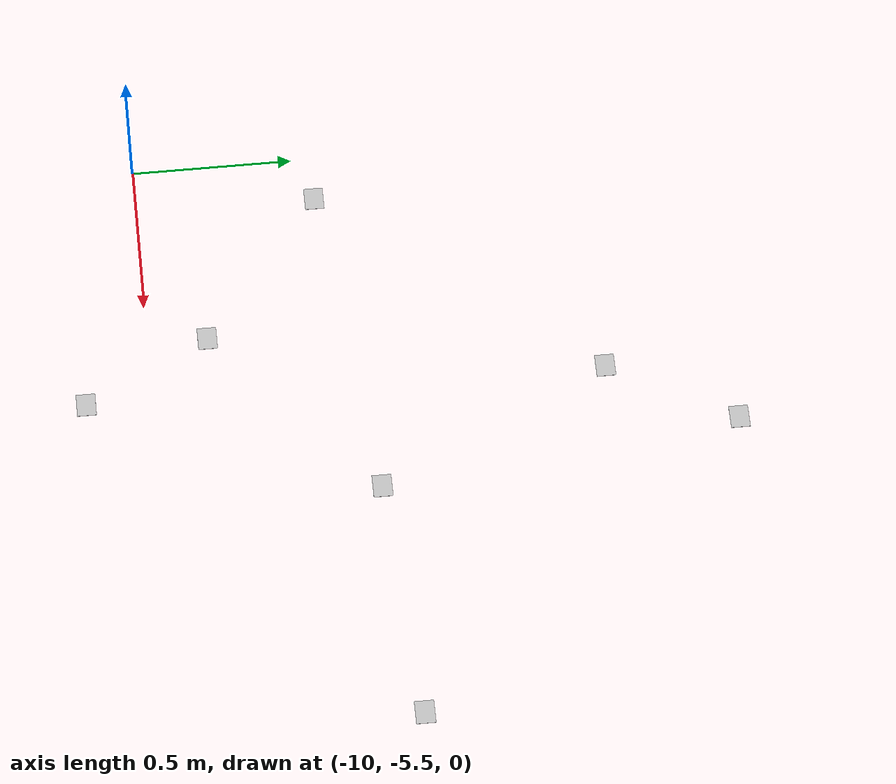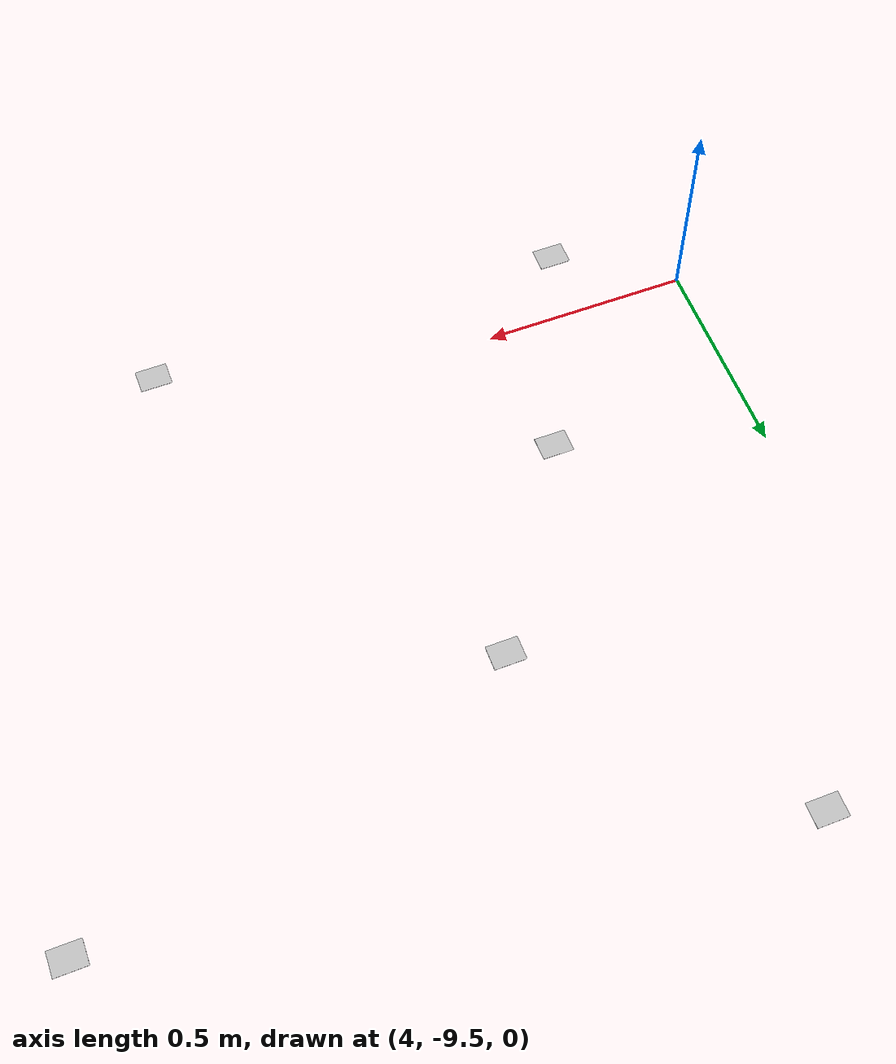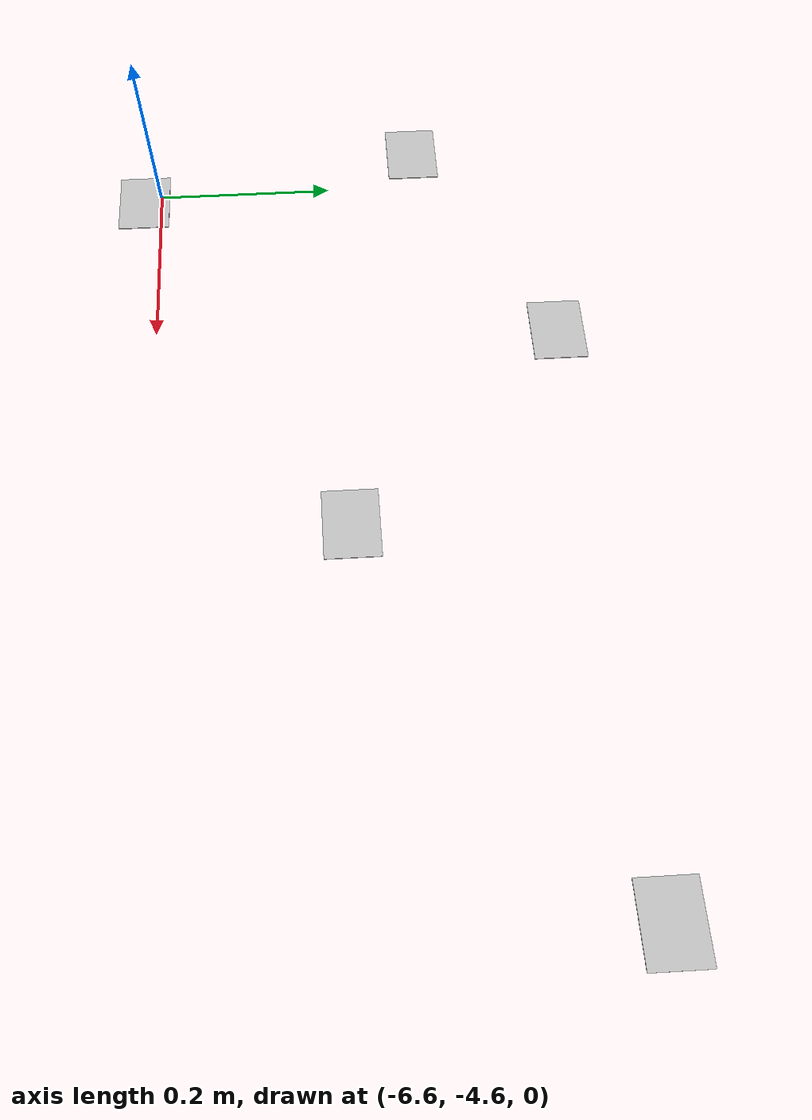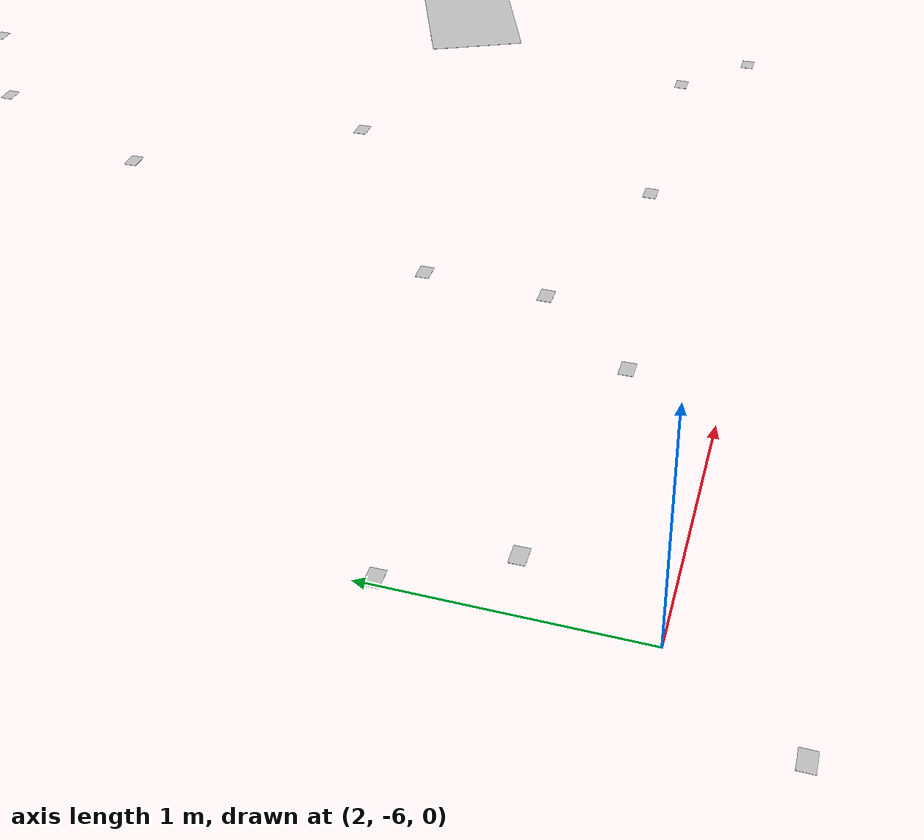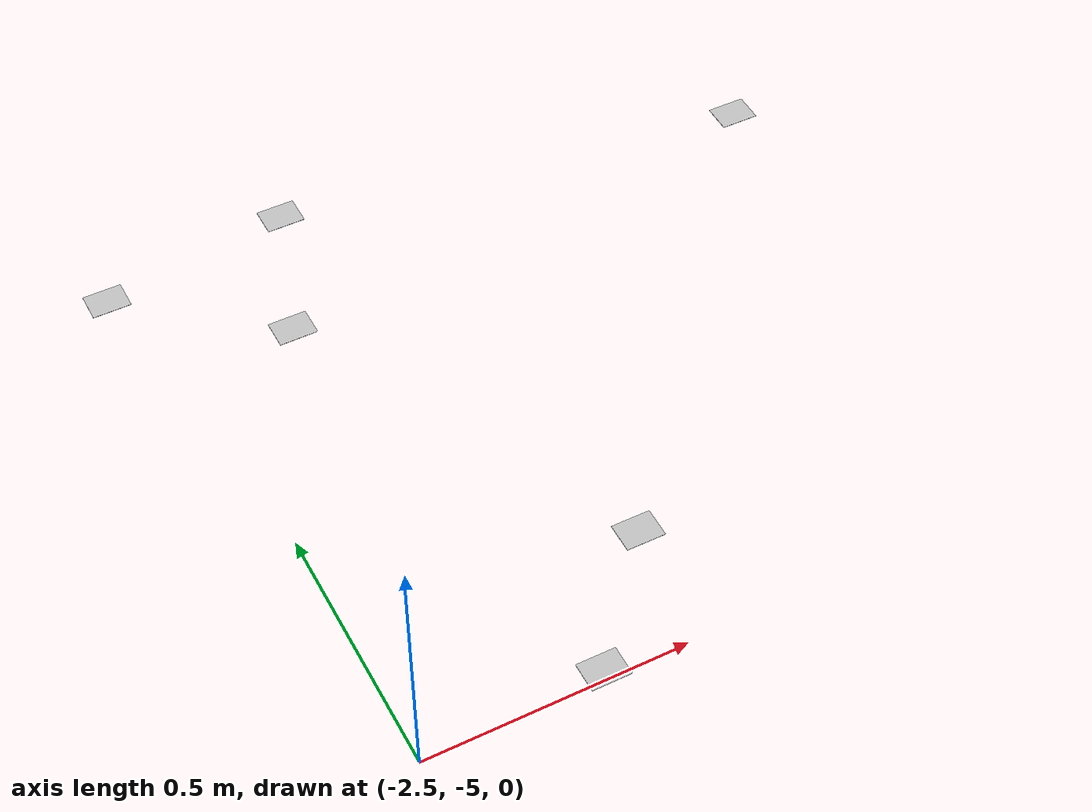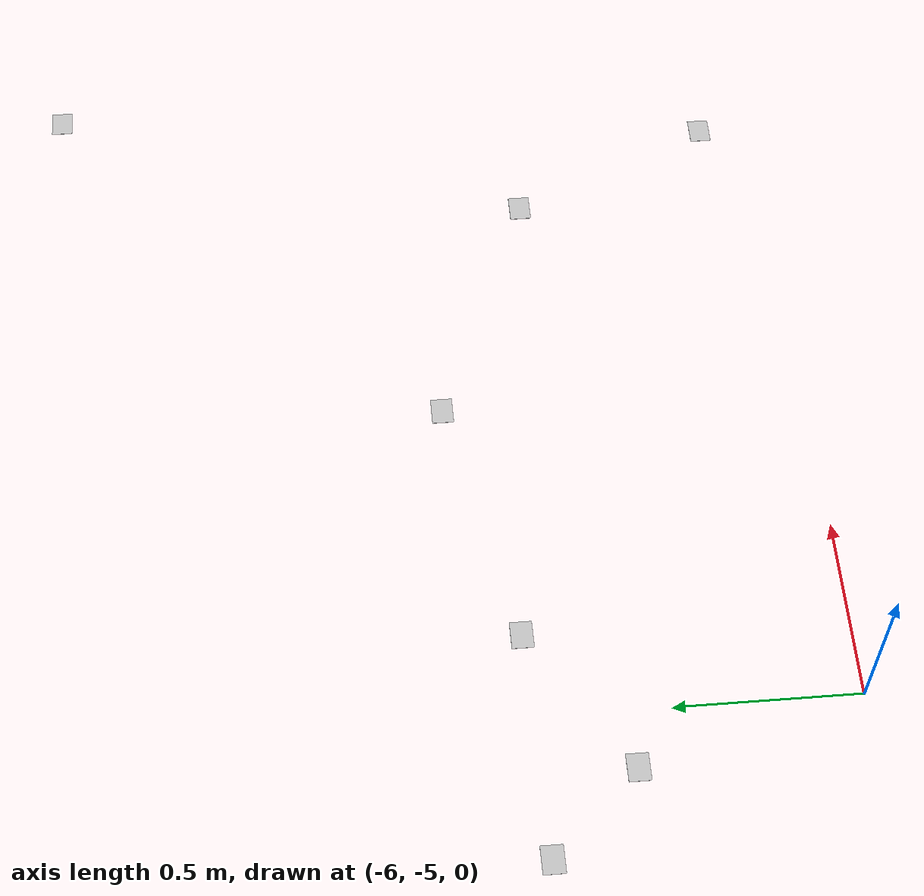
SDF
<sdf version="1.4">
 <world name="default">
  <light name="sun" type="directional">
   <pose>0 0 10 0 -0 0</pose>
   <diffuse>0.8 0.8 0.8 1</diffuse>
   <specular>0.2 0.2 0.2 1</specular>
   <attenuation>
    <range>1000</range>
    <constant>0.9</constant>
    <linear>0.01</linear>
    <quadratic>0.001</quadratic>
   </attenuation>
   <direction>-0.5 0.1 -0.9</direction>
  </light>
  <physics type="ode">
   <max_step_size>0.001</max_step_size>
   <real_time_factor>1</real_time_factor>
   <real_time_update_rate>1000</real_time_update_rate>
   <gravity>0 0 -9.8</gravity>
  </physics>
  <scene><ambient>0.4 0.4 0.4 1</ambient><background>0.7 0.7 0.7 1</background><shadows>1</shadows></scene>
  <spherical_coordinates>
   <surface_model>EARTH_WGS84</surface_model>
   <latitude_deg>0</latitude_deg>
   <longitude_deg>0</longitude_deg>
   <elevation>0</elevation>
   <heading_deg>0</heading_deg>
  </spherical_coordinates>
  <model name="at0">
   <static>1</static>
   <link name="link">
    <collision name="collision"><geometry><box><size>0.0763 0.05912 0.001</size></box></geometry></collision>
    <visual name="visual">
     <geometry><box><size>0.0763 0.05912 0.001</size></box></geometry>
     <material>
      <script>
       <uri>model://at0/materials/scripts</uri>
       <uri>model://at0/materials/textures</uri>
       <name>at1/Diffuse</name>
      </script>
     </material>
    </visual>
    <velocity_decay><linear>0</linear><angular>0</angular></velocity_decay>
   </link>
   <pose>-10.4097 4.31446 0 0 -0 0</pose>
  </model>
  <model name="at1">
   <static>1</static>
   <link name="link">
    <collision name="collision"><geometry><box><size>0.0763 0.05912 0.001</size></box></geometry></collision>
    <visual name="visual">
     <geometry><box><size>0.0763 0.05912 0.001</size></box></geometry>
     <material>
      <script>
       <uri>model://at1/materials/scripts</uri>
       <uri>model://at1/materials/textures</uri>
       <name>at1/Diffuse</name>
      </script>
     </material>
    </visual>
    <velocity_decay><linear>0</linear><angular>0</angular></velocity_decay>
   </link>
   <pose>-10.4097 4.31446 0 0 -0 0</pose>
  </model>
  <model name="at2">
   <static>1</static>
   <link name="link">
    <collision name="collision"><geometry><box><size>0.0763 0.05912 0.001</size></box></geometry></collision>
    <visual name="visual">
     <geometry><box><size>0.0763 0.05912 0.001</size></box></geometry>
     <material>
      <script>
       <uri>model://at2/materials/scripts</uri>
       <uri>model://at2/materials/textures</uri>
       <name>at2/Diffuse</name>
      </script>
     </material>
    </visual>
    <velocity_decay><linear>0</linear><angular>0</angular></velocity_decay>
   </link>
   <pose>-2.91938 -5.9456 0 0 -0 0</pose>
  </model>
  <model name="at3">
   <static>1</static>
   <link name="link">
    <collision name="collision"><geometry><box><size>0.0763 0.05912 0.001</size></box></geometry></collision>
    <visual name="visual">
     <geometry><box><size>0.0763 0.05912 0.001</size></box></geometry>
     <material>
      <script>
       <uri>model://at3/materials/scripts</uri>
       <uri>model://at3/materials/textures</uri>
       <name>at3/Diffuse</name>
      </script>
     </material>
    </visual>
    <velocity_decay><linear>0</linear><angular>0</angular></velocity_decay>
   </link>
   <pose>9.52066 -5.94544 0 0 -0 0</pose>
  </model>
  <model name="at4">
   <static>1</static>
   <link name="link">
    <collision name="collision"><geometry><box><size>0.0763 0.05912 0.001</size></box></geometry></collision>
    <visual name="visual">
     <geometry><box><size>0.0763 0.05912 0.001</size></box></geometry>
     <material>
      <script>
       <uri>model://at4/materials/scripts</uri>
       <uri>model://at4/materials/textures</uri>
       <name>at4/Diffuse</name>
      </script>
     </material>
    </visual>
    <velocity_decay><linear>0</linear><angular>0</angular></velocity_decay>
   </link>
   <pose>-3.55896 4.48625 0 0 -0 0</pose>
  </model>
  <model name="at5">
   <static>1</static>
   <link name="link">
    <collision name="collision"><geometry><box><size>0.0763 0.05912 0.001</size></box></geometry></collision>
    <visual name="visual">
     <geometry><box><size>0.0763 0.05912 0.001</size></box></geometry>
     <material>
      <script>
       <uri>model://at5/materials/scripts</uri>
       <uri>model://at5/materials/textures</uri>
       <name>at5/Diffuse</name>
      </script>
     </material>
    </visual>
    <velocity_decay><linear>0</linear><angular>0</angular></velocity_decay>
   </link>
   <pose>5.03202 -1.75972 0 0 -0 0</pose>
  </model>
  <model name="at6">
   <static>1</static>
   <link name="link">
    <collision name="collision"><geometry><box><size>0.0763 0.05912 0.001</size></box></geometry></collision>
    <visual name="visual">
     <geometry><box><size>0.0763 0.05912 0.001</size></box></geometry>
     <material>
      <script>
       <uri>model://at6/materials/scripts</uri>
       <uri>model://at6/materials/textures</uri>
       <name>at6/Diffuse</name>
      </script>
     </material>
    </visual>
    <velocity_decay><linear>0</linear><angular>0</angular></velocity_decay>
   </link>
   <pose>-3.40009 -7.86494 0 0 -0 0</pose>
  </model>
  <model name="at7">
   <static>1</static>
   <link name="link">
    <collision name="collision"><geometry><box><size>0.0763 0.05912 0.001</size></box></geometry></collision>
    <visual name="visual">
     <geometry><box><size>0.0763 0.05912 0.001</size></box></geometry>
     <material>
      <script>
       <uri>model://at7/materials/scripts</uri>
       <uri>model://at7/materials/textures</uri>
       <name>at7/Diffuse</name>
      </script>
     </material>
    </visual>
    <velocity_decay><linear>0</linear><angular>0</angular></velocity_decay>
   </link>
   <pose>-3.74366 10.031 0 0 -0 0</pose>
  </model>
  <model name="at8">
   <static>1</static>
   <link name="link">
    <collision name="collision"><geometry><box><size>0.0763 0.05912 0.001</size></box></geometry></collision>
    <visual name="visual">
     <geometry><box><size>0.0763 0.05912 0.001</size></box></geometry>
     <material>
      <script>
       <uri>model://at8/materials/scripts</uri>
       <uri>model://at8/materials/textures</uri>
       <name>at8/Diffuse</name>
      </script>
     </material>
    </visual>
    <velocity_decay><linear>0</linear><angular>0</angular></velocity_decay>
   </link>
   <pose>-4.19775 10.3291 0 0 -0 0</pose>
  </model>
  <model name="at9">
   <static>1</static>
   <link name="link">
    <collision name="collision"><geometry><box><size>0.0763 0.05912 0.001</size></box></geometry></collision>
    <visual name="visual">
     <geometry><box><size>0.0763 0.05912 0.001</size></box></geometry>
     <material>
      <script>
       <uri>model://at9/materials/scripts</uri>
       <uri>model://at9/materials/textures</uri>
       <name>at9/Diffuse</name>
      </script>
     </material>
    </visual>
    <velocity_decay><linear>0</linear><angular>0</angular></velocity_decay>
   </link>
   <pose>-1.26052 -3.8954 0 0 -0 0</pose>
  </model>
  <model name="at10">
   <static>1</static>
   <link name="link">
    <collision name="collision"><geometry><box><size>0.0763 0.05912 0.001</size></box></geometry></collision>
    <visual name="visual">
     <geometry><box><size>0.0763 0.05912 0.001</size></box></geometry>
     <material>
      <script>
       <uri>model://at10/materials/scripts</uri>
       <uri>model://at10/materials/textures</uri>
       <name>at10/Diffuse</name>
      </script>
     </material>
    </visual>
    <velocity_decay><linear>0</linear><angular>0</angular></velocity_decay>
   </link>
   <pose>10.3767 -7.51859 0 0 -0 0</pose>
  </model>
  <model name="at11">
   <static>1</static>
   <link name="link">
    <collision name="collision"><geometry><box><size>0.0763 0.05912 0.001</size></box></geometry></collision>
    <visual name="visual">
     <geometry><box><size>0.0763 0.05912 0.001</size></box></geometry>
     <material>
      <script>
       <uri>model://at11/materials/scripts</uri>
       <uri>model://at11/materials/textures</uri>
       <name>at11/Diffuse</name>
      </script>
     </material>
    </visual>
    <velocity_decay><linear>0</linear><angular>0</angular></velocity_decay>
   </link>
   <pose>5.29911 -9.68536 0 0 -0 0</pose>
  </model>
  <model name="at12">
   <static>1</static>
   <link name="link">
    <collision name="collision"><geometry><box><size>0.0763 0.05912 0.001</size></box></geometry></collision>
    <visual name="visual">
     <geometry><box><size>0.0763 0.05912 0.001</size></box></geometry>
     <material>
      <script>
       <uri>model://at12/materials/scripts</uri>
       <uri>model://at12/materials/textures</uri>
       <name>at12/Diffuse</name>
      </script>
     </material>
    </visual>
    <velocity_decay><linear>0</linear><angular>0</angular></velocity_decay>
   </link>
   <pose>3.96837 -1.44841 0 0 -0 0</pose>
  </model>
  <model name="at13">
   <static>1</static>
   <link name="link">
    <collision name="collision"><geometry><box><size>0.0763 0.05912 0.001</size></box></geometry></collision>
    <visual name="visual">
     <geometry><box><size>0.0763 0.05912 0.001</size></box></geometry>
     <material>
      <script>
       <uri>model://at13/materials/scripts</uri>
       <uri>model://at13/materials/textures</uri>
       <name>at13/Diffuse</name>
      </script>
     </material>
    </visual>
    <velocity_decay><linear>0</linear><angular>0</angular></velocity_decay>
   </link>
   <pose>-0.402435 9.13626 0 0 -0 0</pose>
  </model>
  <model name="at14">
   <static>1</static>
   <link name="link">
    <collision name="collision"><geometry><box><size>0.0763 0.05912 0.001</size></box></geometry></collision>
    <visual name="visual">
     <geometry><box><size>0.0763 0.05912 0.001</size></box></geometry>
     <material>
      <script>
       <uri>model://at14/materials/scripts</uri>
       <uri>model://at14/materials/textures</uri>
       <name>at14/Diffuse</name>
      </script>
     </material>
    </visual>
    <velocity_decay><linear>0</linear><angular>0</angular></velocity_decay>
   </link>
   <pose>0.534584 -2.5452 0 0 -0 0</pose>
  </model>
  <model name="at15">
   <static>1</static>
   <link name="link">
    <collision name="collision"><geometry><box><size>0.0763 0.05912 0.001</size></box></geometry></collision>
    <visual name="visual">
     <geometry><box><size>0.0763 0.05912 0.001</size></box></geometry>
     <material>
      <script>
       <uri>model://at15/materials/scripts</uri>
       <uri>model://at15/materials/textures</uri>
       <name>at15/Diffuse</name>
      </script>
     </material>
    </visual>
    <velocity_decay><linear>0</linear><angular>0</angular></velocity_decay>
   </link>
   <pose>-2.52454 -9.9182 0 0 -0 0</pose>
  </model>
  <model name="at16">
   <static>1</static>
   <link name="link">
    <collision name="collision"><geometry><box><size>0.0763 0.05912 0.001</size></box></geometry></collision>
    <visual name="visual">
     <geometry><box><size>0.0763 0.05912 0.001</size></box></geometry>
     <material>
      <script>
       <uri>model://at16/materials/scripts</uri>
       <uri>model://at16/materials/textures</uri>
       <name>at16/Diffuse</name>
      </script>
     </material>
    </visual>
    <velocity_decay><linear>0</linear><angular>0</angular></velocity_decay>
   </link>
   <pose>-6.18131 -1.98419 0 0 -0 0</pose>
  </model>
  <model name="at17">
   <static>1</static>
   <link name="link">
    <collision name="collision"><geometry><box><size>0.0763 0.05912 0.001</size></box></geometry></collision>
    <visual name="visual">
     <geometry><box><size>0.0763 0.05912 0.001</size></box></geometry>
     <material>
      <script>
       <uri>model://at17/materials/scripts</uri>
       <uri>model://at17/materials/textures</uri>
       <name>at17/Diffuse</name>
      </script>
     </material>
    </visual>
    <velocity_decay><linear>0</linear><angular>0</angular></velocity_decay>
   </link>
   <pose>5.34626 1.84931 0 0 -0 0</pose>
  </model>
  <model name="at18">
   <static>1</static>
   <link name="link">
    <collision name="collision"><geometry><box><size>0.0763 0.05912 0.001</size></box></geometry></collision>
    <visual name="visual">
     <geometry><box><size>0.0763 0.05912 0.001</size></box></geometry>
     <material>
      <script>
       <uri>model://at18/materials/scripts</uri>
       <uri>model://at18/materials/textures</uri>
       <name>at18/Diffuse</name>
      </script>
     </material>
    </visual>
    <velocity_decay><linear>0</linear><angular>0</angular></velocity_decay>
   </link>
   <pose>3.0202 3.91692 0 0 -0 0</pose>
  </model>
  <model name="at19">
   <static>1</static>
   <link name="link">
    <collision name="collision"><geometry><box><size>0.0763 0.05912 0.001</size></box></geometry></collision>
    <visual name="visual">
     <geometry><box><size>0.0763 0.05912 0.001</size></box></geometry>
     <material>
      <script>
       <uri>model://at19/materials/scripts</uri>
       <uri>model://at19/materials/textures</uri>
       <name>at19/Diffuse</name>
      </script>
     </material>
    </visual>
    <velocity_decay><linear>0</linear><angular>0</angular></velocity_decay>
   </link>
   <pose>6.85387 10.4112 0 0 -0 0</pose>
  </model>
  <model name="at20">
   <static>1</static>
   <link name="link">
    <collision name="collision"><geometry><box><size>0.0763 0.05912 0.001</size></box></geometry></collision>
    <visual name="visual">
     <geometry><box><size>0.0763 0.05912 0.001</size></box></geometry>
     <material>
      <script>
       <uri>model://at20/materials/scripts</uri>
       <uri>model://at20/materials/textures</uri>
       <name>at20/Diffuse</name>
      </script>
     </material>
    </visual>
    <velocity_decay><linear>0</linear><angular>0</angular></velocity_decay>
   </link>
   <pose>-2.54683 0.935884 0 0 -0 0</pose>
  </model>
  <model name="at21">
   <static>1</static>
   <link name="link">
    <collision name="collision"><geometry><box><size>0.0763 0.05912 0.001</size></box></geometry></collision>
    <visual name="visual">
     <geometry><box><size>0.0763 0.05912 0.001</size></box></geometry>
     <material>
      <script>
       <uri>model://at21/materials/scripts</uri>
       <uri>model://at21/materials/textures</uri>
       <name>at21/Diffuse</name>
      </script>
     </material>
    </visual>
    <velocity_decay><linear>0</linear><angular>0</angular></velocity_decay>
   </link>
   <pose>-2.29847 5.00308 0 0 -0 0</pose>
  </model>
  <model name="at22">
   <static>1</static>
   <link name="link">
    <collision name="collision"><geometry><box><size>0.0763 0.05912 0.001</size></box></geometry></collision>
    <visual name="visual">
     <geometry><box><size>0.0763 0.05912 0.001</size></box></geometry>
     <material>
      <script>
       <uri>model://at22/materials/scripts</uri>
       <uri>model://at22/materials/textures</uri>
       <name>at22/Diffuse</name>
      </script>
     </material>
    </visual>
    <velocity_decay><linear>0</linear><angular>0</angular></velocity_decay>
   </link>
   <pose>4.02094 4.90787 0 0 -0 0</pose>
  </model>
  <model name="at23">
   <static>1</static>
   <link name="link">
    <collision name="collision"><geometry><box><size>0.0763 0.05912 0.001</size></box></geometry></collision>
    <visual name="visual">
     <geometry><box><size>0.0763 0.05912 0.001</size></box></geometry>
     <material>
      <script>
       <uri>model://at23/materials/scripts</uri>
       <uri>model://at23/materials/textures</uri>
       <name>at23/Diffuse</name>
      </script>
     </material>
    </visual>
    <velocity_decay><linear>0</linear><angular>0</angular></velocity_decay>
   </link>
   <pose>4.08409 10.7732 0 0 -0 0</pose>
  </model>
  <model name="at24">
   <static>1</static>
   <link name="link">
    <collision name="collision"><geometry><box><size>0.0763 0.05912 0.001</size></box></geometry></collision>
    <visual name="visual">
     <geometry><box><size>0.0763 0.05912 0.001</size></box></geometry>
     <material>
      <script>
       <uri>model://at24/materials/scripts</uri>
       <uri>model://at24/materials/textures</uri>
       <name>at24/Diffuse</name>
      </script>
     </material>
    </visual>
    <velocity_decay><linear>0</linear><angular>0</angular></velocity_decay>
   </link>
   <pose>4.28696 -8.12643 0 0 -0 0</pose>
  </model>
  <model name="at25">
   <static>1</static>
   <link name="link">
    <collision name="collision"><geometry><box><size>0.0763 0.05912 0.001</size></box></geometry></collision>
    <visual name="visual">
     <geometry><box><size>0.0763 0.05912 0.001</size></box></geometry>
     <material>
      <script>
       <uri>model://at25/materials/scripts</uri>
       <uri>model://at25/materials/textures</uri>
       <name>at25/Diffuse</name>
      </script>
     </material>
    </visual>
    <velocity_decay><linear>0</linear><angular>0</angular></velocity_decay>
   </link>
   <pose>-4.07221 3.71369 0 0 -0 0</pose>
  </model>
  <model name="at26">
   <static>1</static>
   <link name="link">
    <collision name="collision"><geometry><box><size>0.0763 0.05912 0.001</size></box></geometry></collision>
    <visual name="visual">
     <geometry><box><size>0.0763 0.05912 0.001</size></box></geometry>
     <material>
      <script>
       <uri>model://at26/materials/scripts</uri>
       <uri>model://at26/materials/textures</uri>
       <name>at26/Diffuse</name>
      </script>
     </material>
    </visual>
    <velocity_decay><linear>0</linear><angular>0</angular></velocity_decay>
   </link>
   <pose>-4.69502 -9.7231 0 0 -0 0</pose>
  </model>
  <model name="at27">
   <static>1</static>
   <link name="link">
    <collision name="collision"><geometry><box><size>0.0763 0.05912 0.001</size></box></geometry></collision>
    <visual name="visual">
     <geometry><box><size>0.0763 0.05912 0.001</size></box></geometry>
     <material>
      <script>
       <uri>model://at27/materials/scripts</uri>
       <uri>model://at27/materials/textures</uri>
       <name>at27/Diffuse</name>
      </script>
     </material>
    </visual>
    <velocity_decay><linear>0</linear><angular>0</angular></velocity_decay>
   </link>
   <pose>4.97832 10.2233 0 0 -0 0</pose>
  </model>
  <model name="at28">
   <static>1</static>
   <link name="link">
    <collision name="collision"><geometry><box><size>0.0763 0.05912 0.001</size></box></geometry></collision>
    <visual name="visual">
     <geometry><box><size>0.0763 0.05912 0.001</size></box></geometry>
     <material>
      <script>
       <uri>model://at28/materials/scripts</uri>
       <uri>model://at28/materials/textures</uri>
       <name>at28/Diffuse</name>
      </script>
     </material>
    </visual>
    <velocity_decay><linear>0</linear><angular>0</angular></velocity_decay>
   </link>
   <pose>-0.221513 -6.37411 0 0 -0 0</pose>
  </model>
  <model name="at29">
   <static>1</static>
   <link name="link">
    <collision name="collision"><geometry><box><size>0.0763 0.05912 0.001</size></box></geometry></collision>
    <visual name="visual">
     <geometry><box><size>0.0763 0.05912 0.001</size></box></geometry>
     <material>
      <script>
       <uri>model://at29/materials/scripts</uri>
       <uri>model://at29/materials/textures</uri>
       <name>at29/Diffuse</name>
      </script>
     </material>
    </visual>
    <velocity_decay><linear>0</linear><angular>0</angular></velocity_decay>
   </link>
   <pose>8.40961 -10.6369 0 0 -0 0</pose>
  </model>
  <model name="at30">
   <static>1</static>
   <link name="link">
    <collision name="collision"><geometry><box><size>0.0763 0.05912 0.001</size></box></geometry></collision>
    <visual name="visual">
     <geometry><box><size>0.0763 0.05912 0.001</size></box></geometry>
     <material>
      <script>
       <uri>model://at30/materials/scripts</uri>
       <uri>model://at30/materials/textures</uri>
       <name>at30/Diffuse</name>
      </script>
     </material>
    </visual>
    <velocity_decay><linear>0</linear><angular>0</angular></velocity_decay>
   </link>
   <pose>2.03069 -5.06493 0 0 -0 0</pose>
  </model>
  <model name="at31">
   <static>1</static>
   <link name="link">
    <collision name="collision"><geometry><box><size>0.0763 0.05912 0.001</size></box></geometry></collision>
    <visual name="visual">
     <geometry><box><size>0.0763 0.05912 0.001</size></box></geometry>
     <material>
      <script>
       <uri>model://at31/materials/scripts</uri>
       <uri>model://at31/materials/textures</uri>
       <name>at31/Diffuse</name>
      </script>
     </material>
    </visual>
    <velocity_decay><linear>0</linear><angular>0</angular></velocity_decay>
   </link>
   <pose>-9.60513 6.79938 0 0 -0 0</pose>
  </model>
  <model name="at32">
   <static>1</static>
   <link name="link">
    <collision name="collision"><geometry><box><size>0.0763 0.05912 0.001</size></box></geometry></collision>
    <visual name="visual">
     <geometry><box><size>0.0763 0.05912 0.001</size></box></geometry>
     <material>
      <script>
       <uri>model://at32/materials/scripts</uri>
       <uri>model://at32/materials/textures</uri>
       <name>at32/Diffuse</name>
      </script>
     </material>
    </visual>
    <velocity_decay><linear>0</linear><angular>0</angular></velocity_decay>
   </link>
   <pose>3.90087 6.69113 0 0 -0 0</pose>
  </model>
  <model name="at33">
   <static>1</static>
   <link name="link">
    <collision name="collision"><geometry><box><size>0.0763 0.05912 0.001</size></box></geometry></collision>
    <visual name="visual">
     <geometry><box><size>0.0763 0.05912 0.001</size></box></geometry>
     <material>
      <script>
       <uri>model://at33/materials/scripts</uri>
       <uri>model://at33/materials/textures</uri>
       <name>at33/Diffuse</name>
      </script>
     </material>
    </visual>
    <velocity_decay><linear>0</linear><angular>0</angular></velocity_decay>
   </link>
   <pose>-2.30131 -4.02892 0 0 -0 0</pose>
  </model>
  <model name="at34">
   <static>1</static>
   <link name="link">
    <collision name="collision"><geometry><box><size>0.0763 0.05912 0.001</size></box></geometry></collision>
    <visual name="visual">
     <geometry><box><size>0.0763 0.05912 0.001</size></box></geometry>
     <material>
      <script>
       <uri>model://at34/materials/scripts</uri>
       <uri>model://at34/materials/textures</uri>
       <name>at34/Diffuse</name>
      </script>
     </material>
    </visual>
    <velocity_decay><linear>0</linear><angular>0</angular></velocity_decay>
   </link>
   <pose>-4.56768 8.06121 0 0 -0 0</pose>
  </model>
  <model name="at35">
   <static>1</static>
   <link name="link">
    <collision name="collision"><geometry><box><size>0.0763 0.05912 0.001</size></box></geometry></collision>
    <visual name="visual">
     <geometry><box><size>0.0763 0.05912 0.001</size></box></geometry>
     <material>
      <script>
       <uri>model://at35/materials/scripts</uri>
       <uri>model://at35/materials/textures</uri>
       <name>at35/Diffuse</name>
      </script>
     </material>
    </visual>
    <velocity_decay><linear>0</linear><angular>0</angular></velocity_decay>
   </link>
   <pose>5.48844 4.08385 0 0 -0 0</pose>
  </model>
  <model name="at36">
   <static>1</static>
   <link name="link">
    <collision name="collision"><geometry><box><size>0.0763 0.05912 0.001</size></box></geometry></collision>
    <visual name="visual">
     <geometry><box><size>0.0763 0.05912 0.001</size></box></geometry>
     <material>
      <script>
       <uri>model://at36/materials/scripts</uri>
       <uri>model://at36/materials/textures</uri>
       <name>at36/Diffuse</name>
      </script>
     </material>
    </visual>
    <velocity_decay><linear>0</linear><angular>0</angular></velocity_decay>
   </link>
   <pose>2.11429 -1.44062 0 0 -0 0</pose>
  </model>
  <model name="at37">
   <static>1</static>
   <link name="link">
    <collision name="collision"><geometry><box><size>0.0763 0.05912 0.001</size></box></geometry></collision>
    <visual name="visual">
     <geometry><box><size>0.0763 0.05912 0.001</size></box></geometry>
     <material>
      <script>
       <uri>model://at37/materials/scripts</uri>
       <uri>model://at37/materials/textures</uri>
       <name>at37/Diffuse</name>
      </script>
     </material>
    </visual>
    <velocity_decay><linear>0</linear><angular>0</angular></velocity_decay>
   </link>
   <pose>-1.95828 -4.75162 0 0 -0 0</pose>
  </model>
  <model name="at38">
   <static>1</static>
   <link name="link">
    <collision name="collision"><geometry><box><size>0.0763 0.05912 0.001</size></box></geometry></collision>
    <visual name="visual">
     <geometry><box><size>0.0763 0.05912 0.001</size></box></geometry>
     <material>
      <script>
       <uri>model://at38/materials/scripts</uri>
       <uri>model://at38/materials/textures</uri>
       <name>at38/Diffuse</name>
      </script>
     </material>
    </visual>
    <velocity_decay><linear>0</linear><angular>0</angular></velocity_decay>
   </link>
   <pose>-1.61744 -8.62133 0 0 -0 0</pose>
  </model>
  <model name="at39">
   <static>1</static>
   <link name="link">
    <collision name="collision"><geometry><box><size>0.0763 0.05912 0.001</size></box></geometry></collision>
    <visual name="visual">
     <geometry><box><size>0.0763 0.05912 0.001</size></box></geometry>
     <material>
      <script>
       <uri>model://at39/materials/scripts</uri>
       <uri>model://at39/materials/textures</uri>
       <name>at39/Diffuse</name>
      </script>
     </material>
    </visual>
    <velocity_decay><linear>0</linear><angular>0</angular></velocity_decay>
   </link>
   <pose>-1.92806 5.26035 0 0 -0 0</pose>
  </model>
  <model name="at40">
   <static>1</static>
   <link name="link">
    <collision name="collision"><geometry><box><size>0.0763 0.05912 0.001</size></box></geometry></collision>
    <visual name="visual">
     <geometry><box><size>0.0763 0.05912 0.001</size></box></geometry>
     <material>
      <script>
       <uri>model://at40/materials/scripts</uri>
       <uri>model://at40/materials/textures</uri>
       <name>at40/Diffuse</name>
      </script>
     </material>
    </visual>
    <velocity_decay><linear>0</linear><angular>0</angular></velocity_decay>
   </link>
   <pose>6.04236 4.32692 0 0 -0 0</pose>
  </model>
  <model name="at41">
   <static>1</static>
   <link name="link">
    <collision name="collision"><geometry><box><size>0.0763 0.05912 0.001</size></box></geometry></collision>
    <visual name="visual">
     <geometry><box><size>0.0763 0.05912 0.001</size></box></geometry>
     <material>
      <script>
       <uri>model://at41/materials/scripts</uri>
       <uri>model://at41/materials/textures</uri>
       <name>at41/Diffuse</name>
      </script>
     </material>
    </visual>
    <velocity_decay><linear>0</linear><angular>0</angular></velocity_decay>
   </link>
   <pose>6.48726 0.070683 0 0 -0 0</pose>
  </model>
  <model name="at42">
   <static>1</static>
   <link name="link">
    <collision name="collision"><geometry><box><size>0.0763 0.05912 0.001</size></box></geometry></collision>
    <visual name="visual">
     <geometry><box><size>0.0763 0.05912 0.001</size></box></geometry>
     <material>
      <script>
       <uri>model://at42/materials/scripts</uri>
       <uri>model://at42/materials/textures</uri>
       <name>at42/Diffuse</name>
      </script>
     </material>
    </visual>
    <velocity_decay><linear>0</linear><angular>0</angular></velocity_decay>
   </link>
   <pose>3.60027 -4.68426 0 0 -0 0</pose>
  </model>
  <model name="at43">
   <static>1</static>
   <link name="link">
    <collision name="collision"><geometry><box><size>0.0763 0.05912 0.001</size></box></geometry></collision>
    <visual name="visual">
     <geometry><box><size>0.0763 0.05912 0.001</size></box></geometry>
     <material>
      <script>
       <uri>model://at43/materials/scripts</uri>
       <uri>model://at43/materials/textures</uri>
       <name>at43/Diffuse</name>
      </script>
     </material>
    </visual>
    <velocity_decay><linear>0</linear><angular>0</angular></velocity_decay>
   </link>
   <pose>4.64657 1.05988 0 0 -0 0</pose>
  </model>
  <model name="at44">
   <static>1</static>
   <link name="link">
    <collision name="collision"><geometry><box><size>0.0763 0.05912 0.001</size></box></geometry></collision>
    <visual name="visual">
     <geometry><box><size>0.0763 0.05912 0.001</size></box></geometry>
     <material>
      <script>
       <uri>model://at44/materials/scripts</uri>
       <uri>model://at44/materials/textures</uri>
       <name>at44/Diffuse</name>
      </script>
     </material>
    </visual>
    <velocity_decay><linear>0</linear><angular>0</angular></velocity_decay>
   </link>
   <pose>-4.37119 -4.27275 0 0 -0 0</pose>
  </model>
  <model name="at45">
   <static>1</static>
   <link name="link">
    <collision name="collision"><geometry><box><size>0.0763 0.05912 0.001</size></box></geometry></collision>
    <visual name="visual">
     <geometry><box><size>0.0763 0.05912 0.001</size></box></geometry>
     <material>
      <script>
       <uri>model://at45/materials/scripts</uri>
       <uri>model://at45/materials/textures</uri>
       <name>at45/Diffuse</name>
      </script>
     </material>
    </visual>
    <velocity_decay><linear>0</linear><angular>0</angular></velocity_decay>
   </link>
   <pose>6.94495 -3.02632 0 0 -0 0</pose>
  </model>
  <model name="at46">
   <static>1</static>
   <link name="link">
    <collision name="collision"><geometry><box><size>0.0763 0.05912 0.001</size></box></geometry></collision>
    <visual name="visual">
     <geometry><box><size>0.0763 0.05912 0.001</size></box></geometry>
     <material>
      <script>
       <uri>model://at46/materials/scripts</uri>
       <uri>model://at46/materials/textures</uri>
       <name>at46/Diffuse</name>
      </script>
     </material>
    </visual>
    <velocity_decay><linear>0</linear><angular>0</angular></velocity_decay>
   </link>
   <pose>-8.42337 -0.104176 0 0 -0 0</pose>
  </model>
  <model name="at47">
   <static>1</static>
   <link name="link">
    <collision name="collision"><geometry><box><size>0.0763 0.05912 0.001</size></box></geometry></collision>
    <visual name="visual">
     <geometry><box><size>0.0763 0.05912 0.001</size></box></geometry>
     <material>
      <script>
       <uri>model://at47/materials/scripts</uri>
       <uri>model://at47/materials/textures</uri>
       <name>at47/Diffuse</name>
      </script>
     </material>
    </visual>
    <velocity_decay><linear>0</linear><angular>0</angular></velocity_decay>
   </link>
   <pose>-7.28519 0.225318 0 0 -0 0</pose>
  </model>
  <model name="at48">
   <static>1</static>
   <link name="link">
    <collision name="collision"><geometry><box><size>0.0763 0.05912 0.001</size></box></geometry></collision>
    <visual name="visual">
     <geometry><box><size>0.0763 0.05912 0.001</size></box></geometry>
     <material>
      <script>
       <uri>model://at48/materials/scripts</uri>
       <uri>model://at48/materials/textures</uri>
       <name>at48/Diffuse</name>
      </script>
     </material>
    </visual>
    <velocity_decay><linear>0</linear><angular>0</angular></velocity_decay>
   </link>
   <pose>6.8169 3.32285 0 0 -0 0</pose>
  </model>
  <model name="at49">
   <static>1</static>
   <link name="link">
    <collision name="collision"><geometry><box><size>0.0763 0.05912 0.001</size></box></geometry></collision>
    <visual name="visual">
     <geometry><box><size>0.0763 0.05912 0.001</size></box></geometry>
     <material>
      <script>
       <uri>model://at49/materials/scripts</uri>
       <uri>model://at49/materials/textures</uri>
       <name>at49/Diffuse</name>
      </script>
     </material>
    </visual>
    <velocity_decay><linear>0</linear><angular>0</angular></velocity_decay>
   </link>
   <pose>4.77787 -8.70078 0 0 -0 0</pose>
  </model>
  <model name="at50">
   <static>1</static>
   <link name="link">
    <collision name="collision"><geometry><box><size>0.0763 0.05912 0.001</size></box></geometry></collision>
    <visual name="visual">
     <geometry><box><size>0.0763 0.05912 0.001</size></box></geometry>
     <material>
      <script>
       <uri>model://at50/materials/scripts</uri>
       <uri>model://at50/materials/textures</uri>
       <name>at50/Diffuse</name>
      </script>
     </material>
    </visual>
    <velocity_decay><linear>0</linear><angular>0</angular></velocity_decay>
   </link>
   <pose>0.43406 -0.683694 0 0 -0 0</pose>
  </model>
  <model name="at51">
   <static>1</static>
   <link name="link">
    <collision name="collision"><geometry><box><size>0.0763 0.05912 0.001</size></box></geometry></collision>
    <visual name="visual">
     <geometry><box><size>0.0763 0.05912 0.001</size></box></geometry>
     <material>
      <script>
       <uri>model://at51/materials/scripts</uri>
       <uri>model://at51/materials/textures</uri>
       <name>at51/Diffuse</name>
      </script>
     </material>
    </visual>
    <velocity_decay><linear>0</linear><angular>0</angular></velocity_decay>
   </link>
   <pose>6.33308 -8.40165 0 0 -0 0</pose>
  </model>
  <model name="at52">
   <static>1</static>
   <link name="link">
    <collision name="collision"><geometry><box><size>0.0763 0.05912 0.001</size></box></geometry></collision>
    <visual name="visual">
     <geometry><box><size>0.0763 0.05912 0.001</size></box></geometry>
     <material>
      <script>
       <uri>model://at52/materials/scripts</uri>
       <uri>model://at52/materials/textures</uri>
       <name>at52/Diffuse</name>
      </script>
     </material>
    </visual>
    <velocity_decay><linear>0</linear><angular>0</angular></velocity_decay>
   </link>
   <pose>8.82568 -6.57521 0 0 -0 0</pose>
  </model>
  <model name="at53">
   <static>1</static>
   <link name="link">
    <collision name="collision"><geometry><box><size>0.0763 0.05912 0.001</size></box></geometry></collision>
    <visual name="visual">
     <geometry><box><size>0.0763 0.05912 0.001</size></box></geometry>
     <material>
      <script>
       <uri>model://at53/materials/scripts</uri>
       <uri>model://at53/materials/textures</uri>
       <name>at53/Diffuse</name>
      </script>
     </material>
    </visual>
    <velocity_decay><linear>0</linear><angular>0</angular></velocity_decay>
   </link>
   <pose>-2.20327 -3.74175 0 0 -0 0</pose>
  </model>
  <model name="at54">
   <static>1</static>
   <link name="link">
    <collision name="collision"><geometry><box><size>0.0763 0.05912 0.001</size></box></geometry></collision>
    <visual name="visual">
     <geometry><box><size>0.0763 0.05912 0.001</size></box></geometry>
     <material>
      <script>
       <uri>model://at54/materials/scripts</uri>
       <uri>model://at54/materials/textures</uri>
       <name>at54/Diffuse</name>
      </script>
     </material>
    </visual>
    <velocity_decay><linear>0</linear><angular>0</angular></velocity_decay>
   </link>
   <pose>-4.24653 6.81867 0 0 -0 0</pose>
  </model>
  <model name="at55">
   <static>1</static>
   <link name="link">
    <collision name="collision"><geometry><box><size>0.0763 0.05912 0.001</size></box></geometry></collision>
    <visual name="visual">
     <geometry><box><size>0.0763 0.05912 0.001</size></box></geometry>
     <material>
      <script>
       <uri>model://at55/materials/scripts</uri>
       <uri>model://at55/materials/textures</uri>
       <name>at55/Diffuse</name>
      </script>
     </material>
    </visual>
    <velocity_decay><linear>0</linear><angular>0</angular></velocity_decay>
   </link>
   <pose>-9.4314 -9.15417 0 0 -0 0</pose>
  </model>
  <model name="at56">
   <static>1</static>
   <link name="link">
    <collision name="collision"><geometry><box><size>0.0763 0.05912 0.001</size></box></geometry></collision>
    <visual name="visual">
     <geometry><box><size>0.0763 0.05912 0.001</size></box></geometry>
     <material>
      <script>
       <uri>model://at56/materials/scripts</uri>
       <uri>model://at56/materials/textures</uri>
       <name>at56/Diffuse</name>
      </script>
     </material>
    </visual>
    <velocity_decay><linear>0</linear><angular>0</angular></velocity_decay>
   </link>
   <pose>0.195592 8.00586 0 0 -0 0</pose>
  </model>
  <model name="at57">
   <static>1</static>
   <link name="link">
    <collision name="collision"><geometry><box><size>0.0763 0.05912 0.001</size></box></geometry></collision>
    <visual name="visual">
     <geometry><box><size>0.0763 0.05912 0.001</size></box></geometry>
     <material>
      <script>
       <uri>model://at57/materials/scripts</uri>
       <uri>model://at57/materials/textures</uri>
       <name>at57/Diffuse</name>
      </script>
     </material>
    </visual>
    <velocity_decay><linear>0</linear><angular>0</angular></velocity_decay>
   </link>
   <pose>1.86651 -7.15414 0 0 -0 0</pose>
  </model>
  <model name="at58">
   <static>1</static>
   <link name="link">
    <collision name="collision"><geometry><box><size>0.0763 0.05912 0.001</size></box></geometry></collision>
    <visual name="visual">
     <geometry><box><size>0.0763 0.05912 0.001</size></box></geometry>
     <material>
      <script>
       <uri>model://at58/materials/scripts</uri>
       <uri>model://at58/materials/textures</uri>
       <name>at58/Diffuse</name>
      </script>
     </material>
    </visual>
    <velocity_decay><linear>0</linear><angular>0</angular></velocity_decay>
   </link>
   <pose>-7.6284 -4.43692 0 0 -0 0</pose>
  </model>
  <model name="at59">
   <static>1</static>
   <link name="link">
    <collision name="collision"><geometry><box><size>0.0763 0.05912 0.001</size></box></geometry></collision>
    <visual name="visual">
     <geometry><box><size>0.0763 0.05912 0.001</size></box></geometry>
     <material>
      <script>
       <uri>model://at59/materials/scripts</uri>
       <uri>model://at59/materials/textures</uri>
       <name>at59/Diffuse</name>
      </script>
     </material>
    </visual>
    <velocity_decay><linear>0</linear><angular>0</angular></velocity_decay>
   </link>
   <pose>4.85574 -1.04958 0 0 -0 0</pose>
  </model>
  <model name="at60">
   <static>1</static>
   <link name="link">
    <collision name="collision"><geometry><box><size>0.0763 0.05912 0.001</size></box></geometry></collision>
    <visual name="visual">
     <geometry><box><size>0.0763 0.05912 0.001</size></box></geometry>
     <material>
      <script>
       <uri>model://at60/materials/scripts</uri>
       <uri>model://at60/materials/textures</uri>
       <name>at60/Diffuse</name>
      </script>
     </material>
    </visual>
    <velocity_decay><linear>0</linear><angular>0</angular></velocity_decay>
   </link>
   <pose>2.24034 0.850692 0 0 -0 0</pose>
  </model>
  <model name="at61">
   <static>1</static>
   <link name="link">
    <collision name="collision"><geometry><box><size>0.0763 0.05912 0.001</size></box></geometry></collision>
    <visual name="visual">
     <geometry><box><size>0.0763 0.05912 0.001</size></box></geometry>
     <material>
      <script>
       <uri>model://at61/materials/scripts</uri>
       <uri>model://at61/materials/textures</uri>
       <name>at61/Diffuse</name>
      </script>
     </material>
    </visual>
    <velocity_decay><linear>0</linear><angular>0</angular></velocity_decay>
   </link>
   <pose>6.8741 4.76697 0 0 -0 0</pose>
  </model>
  <model name="at62">
   <static>1</static>
   <link name="link">
    <collision name="collision"><geometry><box><size>0.0763 0.05912 0.001</size></box></geometry></collision>
    <visual name="visual">
     <geometry><box><size>0.0763 0.05912 0.001</size></box></geometry>
     <material>
      <script>
       <uri>model://at62/materials/scripts</uri>
       <uri>model://at62/materials/textures</uri>
       <name>at62/Diffuse</name>
      </script>
     </material>
    </visual>
    <velocity_decay><linear>0</linear><angular>0</angular></velocity_decay>
   </link>
   <pose>-10.2035 10.5389 0 0 -0 0</pose>
  </model>
  <model name="at63">
   <static>1</static>
   <link name="link">
    <collision name="collision"><geometry><box><size>0.0763 0.05912 0.001</size></box></geometry></collision>
    <visual name="visual">
     <geometry><box><size>0.0763 0.05912 0.001</size></box></geometry>
     <material>
      <script>
       <uri>model://at63/materials/scripts</uri>
       <uri>model://at63/materials/textures</uri>
       <name>at63/Diffuse</name>
      </script>
     </material>
    </visual>
    <velocity_decay><linear>0</linear><angular>0</angular></velocity_decay>
   </link>
   <pose>-5.95771 7.56342 0 0 -0 0</pose>
  </model>
  <model name="at64">
   <static>1</static>
   <link name="link">
    <collision name="collision"><geometry><box><size>0.0763 0.05912 0.001</size></box></geometry></collision>
    <visual name="visual">
     <geometry><box><size>0.0763 0.05912 0.001</size></box></geometry>
     <material>
      <script>
       <uri>model://at64/materials/scripts</uri>
       <uri>model://at64/materials/textures</uri>
       <name>at64/Diffuse</name>
      </script>
     </material>
    </visual>
    <velocity_decay><linear>0</linear><angular>0</angular></velocity_decay>
   </link>
   <pose>2.91175 9.77016 0 0 -0 0</pose>
  </model>
  <model name="at65">
   <static>1</static>
   <link name="link">
    <collision name="collision"><geometry><box><size>0.0763 0.05912 0.001</size></box></geometry></collision>
    <visual name="visual">
     <geometry><box><size>0.0763 0.05912 0.001</size></box></geometry>
     <material>
      <script>
       <uri>model://at65/materials/scripts</uri>
       <uri>model://at65/materials/textures</uri>
       <name>at65/Diffuse</name>
      </script>
     </material>
    </visual>
    <velocity_decay><linear>0</linear><angular>0</angular></velocity_decay>
   </link>
   <pose>9.81264 -7.60419 0 0 -0 0</pose>
  </model>
  <model name="at66">
   <static>1</static>
   <link name="link">
    <collision name="collision"><geometry><box><size>0.0763 0.05912 0.001</size></box></geometry></collision>
    <visual name="visual">
     <geometry><box><size>0.0763 0.05912 0.001</size></box></geometry>
     <material>
      <script>
       <uri>model://at66/materials/scripts</uri>
       <uri>model://at66/materials/textures</uri>
       <name>at66/Diffuse</name>
      </script>
     </material>
    </visual>
    <velocity_decay><linear>0</linear><angular>0</angular></velocity_decay>
   </link>
   <pose>-5.05583 -3.98785 0 0 -0 0</pose>
  </model>
  <model name="at67">
   <static>1</static>
   <link name="link">
    <collision name="collision"><geometry><box><size>0.0763 0.05912 0.001</size></box></geometry></collision>
    <visual name="visual">
     <geometry><box><size>0.0763 0.05912 0.001</size></box></geometry>
     <material>
      <script>
       <uri>model://at67/materials/scripts</uri>
       <uri>model://at67/materials/textures</uri>
       <name>at67/Diffuse</name>
      </script>
     </material>
    </visual>
    <velocity_decay><linear>0</linear><angular>0</angular></velocity_decay>
   </link>
   <pose>9.57051 3.69089 0 0 -0 0</pose>
  </model>
  <model name="at68">
   <static>1</static>
   <link name="link">
    <collision name="collision"><geometry><box><size>0.0763 0.05912 0.001</size></box></geometry></collision>
    <visual name="visual">
     <geometry><box><size>0.0763 0.05912 0.001</size></box></geometry>
     <material>
      <script>
       <uri>model://at68/materials/scripts</uri>
       <uri>model://at68/materials/textures</uri>
       <name>at68/Diffuse</name>
      </script>
     </material>
    </visual>
    <velocity_decay><linear>0</linear><angular>0</angular></velocity_decay>
   </link>
   <pose>3.2204 -5.62602 0 0 -0 0</pose>
  </model>
  <model name="at69">
   <static>1</static>
   <link name="link">
    <collision name="collision"><geometry><box><size>0.0763 0.05912 0.001</size></box></geometry></collision>
    <visual name="visual">
     <geometry><box><size>0.0763 0.05912 0.001</size></box></geometry>
     <material>
      <script>
       <uri>model://at69/materials/scripts</uri>
       <uri>model://at69/materials/textures</uri>
       <name>at69/Diffuse</name>
      </script>
     </material>
    </visual>
    <velocity_decay><linear>0</linear><angular>0</angular></velocity_decay>
   </link>
   <pose>-0.440435 4.739 0 0 -0 0</pose>
  </model>
  <model name="at70">
   <static>1</static>
   <link name="link">
    <collision name="collision"><geometry><box><size>0.0763 0.05912 0.001</size></box></geometry></collision>
    <visual name="visual">
     <geometry><box><size>0.0763 0.05912 0.001</size></box></geometry>
     <material>
      <script>
       <uri>model://at70/materials/scripts</uri>
       <uri>model://at70/materials/textures</uri>
       <name>at70/Diffuse</name>
      </script>
     </material>
    </visual>
    <velocity_decay><linear>0</linear><angular>0</angular></velocity_decay>
   </link>
   <pose>-3.83019 10.7052 0 0 -0 0</pose>
  </model>
  <model name="at71">
   <static>1</static>
   <link name="link">
    <collision name="collision"><geometry><box><size>0.0763 0.05912 0.001</size></box></geometry></collision>
    <visual name="visual">
     <geometry><box><size>0.0763 0.05912 0.001</size></box></geometry>
     <material>
      <script>
       <uri>model://at71/materials/scripts</uri>
       <uri>model://at71/materials/textures</uri>
       <name>at71/Diffuse</name>
      </script>
     </material>
    </visual>
    <velocity_decay><linear>0</linear><angular>0</angular></velocity_decay>
   </link>
   <pose>1.79486 8.98633 0 0 -0 0</pose>
  </model>
  <model name="at72">
   <static>1</static>
   <link name="link">
    <collision name="collision"><geometry><box><size>0.0763 0.05912 0.001</size></box></geometry></collision>
    <visual name="visual">
     <geometry><box><size>0.0763 0.05912 0.001</size></box></geometry>
     <material>
      <script>
       <uri>model://at72/materials/scripts</uri>
       <uri>model://at72/materials/textures</uri>
       <name>at72/Diffuse</name>
      </script>
     </material>
    </visual>
    <velocity_decay><linear>0</linear><angular>0</angular></velocity_decay>
   </link>
   <pose>-7.39898 5.11646 0 0 -0 0</pose>
  </model>
  <model name="at73">
   <static>1</static>
   <link name="link">
    <collision name="collision"><geometry><box><size>0.0763 0.05912 0.001</size></box></geometry></collision>
    <visual name="visual">
     <geometry><box><size>0.0763 0.05912 0.001</size></box></geometry>
     <material>
      <script>
       <uri>model://at73/materials/scripts</uri>
       <uri>model://at73/materials/textures</uri>
       <name>at73/Diffuse</name>
      </script>
     </material>
    </visual>
    <velocity_decay><linear>0</linear><angular>0</angular></velocity_decay>
   </link>
   <pose>-6.40059 8.40676 0 0 -0 0</pose>
  </model>
  <model name="at74">
   <static>1</static>
   <link name="link">
    <collision name="collision"><geometry><box><size>0.0763 0.05912 0.001</size></box></geometry></collision>
    <visual name="visual">
     <geometry><box><size>0.0763 0.05912 0.001</size></box></geometry>
     <material>
      <script>
       <uri>model://at74/materials/scripts</uri>
       <uri>model://at74/materials/textures</uri>
       <name>at74/Diffuse</name>
      </script>
     </material>
    </visual>
    <velocity_decay><linear>0</linear><angular>0</angular></velocity_decay>
   </link>
   <pose>-6.88312 6.78975 0 0 -0 0</pose>
  </model>
  <model name="at75">
   <static>1</static>
   <link name="link">
    <collision name="collision"><geometry><box><size>0.0763 0.05912 0.001</size></box></geometry></collision>
    <visual name="visual">
     <geometry><box><size>0.0763 0.05912 0.001</size></box></geometry>
     <material>
      <script>
       <uri>model://at75/materials/scripts</uri>
       <uri>model://at75/materials/textures</uri>
       <name>at75/Diffuse</name>
      </script>
     </material>
    </visual>
    <velocity_decay><linear>0</linear><angular>0</angular></velocity_decay>
   </link>
   <pose>-1.69255 10.941 0 0 -0 0</pose>
  </model>
  <model name="at76">
   <static>1</static>
   <link name="link">
    <collision name="collision"><geometry><box><size>0.0763 0.05912 0.001</size></box></geometry></collision>
    <visual name="visual">
     <geometry><box><size>0.0763 0.05912 0.001</size></box></geometry>
     <material>
      <script>
       <uri>model://at76/materials/scripts</uri>
       <uri>model://at76/materials/textures</uri>
       <name>at76/Diffuse</name>
      </script>
     </material>
    </visual>
    <velocity_decay><linear>0</linear><angular>0</angular></velocity_decay>
   </link>
   <pose>10.5299 5.59901 0 0 -0 0</pose>
  </model>
  <model name="at77">
   <static>1</static>
   <link name="link">
    <collision name="collision"><geometry><box><size>0.0763 0.05912 0.001</size></box></geometry></collision>
    <visual name="visual">
     <geometry><box><size>0.0763 0.05912 0.001</size></box></geometry>
     <material>
      <script>
       <uri>model://at77/materials/scripts</uri>
       <uri>model://at77/materials/textures</uri>
       <name>at77/Diffuse</name>
      </script>
     </material>
    </visual>
    <velocity_decay><linear>0</linear><angular>0</angular></velocity_decay>
   </link>
   <pose>-4.33261 2.49163 0 0 -0 0</pose>
  </model>
  <model name="at78">
   <static>1</static>
   <link name="link">
    <collision name="collision"><geometry><box><size>0.0763 0.05912 0.001</size></box></geometry></collision>
    <visual name="visual">
     <geometry><box><size>0.0763 0.05912 0.001</size></box></geometry>
     <material>
      <script>
       <uri>model://at78/materials/scripts</uri>
       <uri>model://at78/materials/textures</uri>
       <name>at78/Diffuse</name>
      </script>
     </material>
    </visual>
    <velocity_decay><linear>0</linear><angular>0</angular></velocity_decay>
   </link>
   <pose>4.41917 -5.46997 0 0 -0 0</pose>
  </model>
  <model name="at79">
   <static>1</static>
   <link name="link">
    <collision name="collision"><geometry><box><size>0.0763 0.05912 0.001</size></box></geometry></collision>
    <visual name="visual">
     <geometry><box><size>0.0763 0.05912 0.001</size></box></geometry>
     <material>
      <script>
       <uri>model://at79/materials/scripts</uri>
       <uri>model://at79/materials/textures</uri>
       <name>at79/Diffuse</name>
      </script>
     </material>
    </visual>
    <velocity_decay><linear>0</linear><angular>0</angular></velocity_decay>
   </link>
   <pose>5.83744 -8.39436 0 0 -0 0</pose>
  </model>
  <model name="at80">
   <static>1</static>
   <link name="link">
    <collision name="collision"><geometry><box><size>0.0763 0.05912 0.001</size></box></geometry></collision>
    <visual name="visual">
     <geometry><box><size>0.0763 0.05912 0.001</size></box></geometry>
     <material>
      <script>
       <uri>model://at80/materials/scripts</uri>
       <uri>model://at80/materials/textures</uri>
       <name>at80/Diffuse</name>
      </script>
     </material>
    </visual>
    <velocity_decay><linear>0</linear><angular>0</angular></velocity_decay>
   </link>
   <pose>10.6757 -10.1684 0 0 -0 0</pose>
  </model>
  <model name="at81">
   <static>1</static>
   <link name="link">
    <collision name="collision"><geometry><box><size>0.0763 0.05912 0.001</size></box></geometry></collision>
    <visual name="visual">
     <geometry><box><size>0.0763 0.05912 0.001</size></box></geometry>
     <material>
      <script>
       <uri>model://at81/materials/scripts</uri>
       <uri>model://at81/materials/textures</uri>
       <name>at81/Diffuse</name>
      </script>
     </material>
    </visual>
    <velocity_decay><linear>0</linear><angular>0</angular></velocity_decay>
   </link>
   <pose>-1.43221 9.29625 0 0 -0 0</pose>
  </model>
  <model name="at82">
   <static>1</static>
   <link name="link">
    <collision name="collision"><geometry><box><size>0.0763 0.05912 0.001</size></box></geometry></collision>
    <visual name="visual">
     <geometry><box><size>0.0763 0.05912 0.001</size></box></geometry>
     <material>
      <script>
       <uri>model://at82/materials/scripts</uri>
       <uri>model://at82/materials/textures</uri>
       <name>at82/Diffuse</name>
      </script>
     </material>
    </visual>
    <velocity_decay><linear>0</linear><angular>0</angular></velocity_decay>
   </link>
   <pose>4.4725 -9.16181 0 0 -0 0</pose>
  </model>
  <model name="at83">
   <static>1</static>
   <link name="link">
    <collision name="collision"><geometry><box><size>0.0763 0.05912 0.001</size></box></geometry></collision>
    <visual name="visual">
     <geometry><box><size>0.0763 0.05912 0.001</size></box></geometry>
     <material>
      <script>
       <uri>model://at83/materials/scripts</uri>
       <uri>model://at83/materials/textures</uri>
       <name>at83/Diffuse</name>
      </script>
     </material>
    </visual>
    <velocity_decay><linear>0</linear><angular>0</angular></velocity_decay>
   </link>
   <pose>-7.27977 -6.91793 0 0 -0 0</pose>
  </model>
  <model name="at84">
   <static>1</static>
   <link name="link">
    <collision name="collision"><geometry><box><size>0.0763 0.05912 0.001</size></box></geometry></collision>
    <visual name="visual">
     <geometry><box><size>0.0763 0.05912 0.001</size></box></geometry>
     <material>
      <script>
       <uri>model://at84/materials/scripts</uri>
       <uri>model://at84/materials/textures</uri>
       <name>at84/Diffuse</name>
      </script>
     </material>
    </visual>
    <velocity_decay><linear>0</linear><angular>0</angular></velocity_decay>
   </link>
   <pose>6.52719 -0.159957 0 0 -0 0</pose>
  </model>
  <model name="at85">
   <static>1</static>
   <link name="link">
    <collision name="collision"><geometry><box><size>0.0763 0.05912 0.001</size></box></geometry></collision>
    <visual name="visual">
     <geometry><box><size>0.0763 0.05912 0.001</size></box></geometry>
     <material>
      <script>
       <uri>model://at85/materials/scripts</uri>
       <uri>model://at85/materials/textures</uri>
       <name>at85/Diffuse</name>
      </script>
     </material>
    </visual>
    <velocity_decay><linear>0</linear><angular>0</angular></velocity_decay>
   </link>
   <pose>-7.16278 -2.62794 0 0 -0 0</pose>
  </model>
  <model name="at86">
   <static>1</static>
   <link name="link">
    <collision name="collision"><geometry><box><size>0.0763 0.05912 0.001</size></box></geometry></collision>
    <visual name="visual">
     <geometry><box><size>0.0763 0.05912 0.001</size></box></geometry>
     <material>
      <script>
       <uri>model://at86/materials/scripts</uri>
       <uri>model://at86/materials/textures</uri>
       <name>at86/Diffuse</name>
      </script>
     </material>
    </visual>
    <velocity_decay><linear>0</linear><angular>0</angular></velocity_decay>
   </link>
   <pose>-8.46148 2.42578 0 0 -0 0</pose>
  </model>
  <model name="at87">
   <static>1</static>
   <link name="link">
    <collision name="collision"><geometry><box><size>0.0763 0.05912 0.001</size></box></geometry></collision>
    <visual name="visual">
     <geometry><box><size>0.0763 0.05912 0.001</size></box></geometry>
     <material>
      <script>
       <uri>model://at87/materials/scripts</uri>
       <uri>model://at87/materials/textures</uri>
       <name>at87/Diffuse</name>
      </script>
     </material>
    </visual>
    <velocity_decay><linear>0</linear><angular>0</angular></velocity_decay>
   </link>
   <pose>-6.15499 -4.3946 0 0 -0 0</pose>
  </model>
  <model name="at88">
   <static>1</static>
   <link name="link">
    <collision name="collision"><geometry><box><size>0.0763 0.05912 0.001</size></box></geometry></collision>
    <visual name="visual">
     <geometry><box><size>0.0763 0.05912 0.001</size></box></geometry>
     <material>
      <script>
       <uri>model://at88/materials/scripts</uri>
       <uri>model://at88/materials/textures</uri>
       <name>at88/Diffuse</name>
      </script>
     </material>
    </visual>
    <velocity_decay><linear>0</linear><angular>0</angular></velocity_decay>
   </link>
   <pose>-1.73447 3.10246 0 0 -0 0</pose>
  </model>
  <model name="at89">
   <static>1</static>
   <link name="link">
    <collision name="collision"><geometry><box><size>0.0763 0.05912 0.001</size></box></geometry></collision>
    <visual name="visual">
     <geometry><box><size>0.0763 0.05912 0.001</size></box></geometry>
     <material>
      <script>
       <uri>model://at89/materials/scripts</uri>
       <uri>model://at89/materials/textures</uri>
       <name>at89/Diffuse</name>
      </script>
     </material>
    </visual>
    <velocity_decay><linear>0</linear><angular>0</angular></velocity_decay>
   </link>
   <pose>-4.40363 9.82225 0 0 -0 0</pose>
  </model>
  <model name="at90">
   <static>1</static>
   <link name="link">
    <collision name="collision"><geometry><box><size>0.0763 0.05912 0.001</size></box></geometry></collision>
    <visual name="visual">
     <geometry><box><size>0.0763 0.05912 0.001</size></box></geometry>
     <material>
      <script>
       <uri>model://at90/materials/scripts</uri>
       <uri>model://at90/materials/textures</uri>
       <name>at90/Diffuse</name>
      </script>
     </material>
    </visual>
    <velocity_decay><linear>0</linear><angular>0</angular></velocity_decay>
   </link>
   <pose>-8.79357 -4.82375 0 0 -0 0</pose>
  </model>
  <model name="at91">
   <static>1</static>
   <link name="link">
    <collision name="collision"><geometry><box><size>0.0763 0.05912 0.001</size></box></geometry></collision>
    <visual name="visual">
     <geometry><box><size>0.0763 0.05912 0.001</size></box></geometry>
     <material>
      <script>
       <uri>model://at91/materials/scripts</uri>
       <uri>model://at91/materials/textures</uri>
       <name>at91/Diffuse</name>
      </script>
     </material>
    </visual>
    <velocity_decay><linear>0</linear><angular>0</angular></velocity_decay>
   </link>
   <pose>4.47126 -2.17618 0 0 -0 0</pose>
  </model>
  <model name="at92">
   <static>1</static>
   <link name="link">
    <collision name="collision"><geometry><box><size>0.0763 0.05912 0.001</size></box></geometry></collision>
    <visual name="visual">
     <geometry><box><size>0.0763 0.05912 0.001</size></box></geometry>
     <material>
      <script>
       <uri>model://at92/materials/scripts</uri>
       <uri>model://at92/materials/textures</uri>
       <name>at92/Diffuse</name>
      </script>
     </material>
    </visual>
    <velocity_decay><linear>0</linear><angular>0</angular></velocity_decay>
   </link>
   <pose>8.61789 -2.05957 0 0 -0 0</pose>
  </model>
  <model name="at93">
   <static>1</static>
   <link name="link">
    <collision name="collision"><geometry><box><size>0.0763 0.05912 0.001</size></box></geometry></collision>
    <visual name="visual">
     <geometry><box><size>0.0763 0.05912 0.001</size></box></geometry>
     <material>
      <script>
       <uri>model://at93/materials/scripts</uri>
       <uri>model://at93/materials/textures</uri>
       <name>at93/Diffuse</name>
      </script>
     </material>
    </visual>
    <velocity_decay><linear>0</linear><angular>0</angular></velocity_decay>
   </link>
   <pose>3.30384 3.50533 0 0 -0 0</pose>
  </model>
  <model name="at94">
   <static>1</static>
   <link name="link">
    <collision name="collision"><geometry><box><size>0.0763 0.05912 0.001</size></box></geometry></collision>
    <visual name="visual">
     <geometry><box><size>0.0763 0.05912 0.001</size></box></geometry>
     <material>
      <script>
       <uri>model://at94/materials/scripts</uri>
       <uri>model://at94/materials/textures</uri>
       <name>at94/Diffuse</name>
      </script>
     </material>
    </visual>
    <velocity_decay><linear>0</linear><angular>0</angular></velocity_decay>
   </link>
   <pose>0.496063 3.02959 0 0 -0 0</pose>
  </model>
  <model name="at95">
   <static>1</static>
   <link name="link">
    <collision name="collision"><geometry><box><size>0.0763 0.05912 0.001</size></box></geometry></collision>
    <visual name="visual">
     <geometry><box><size>0.0763 0.05912 0.001</size></box></geometry>
     <material>
      <script>
       <uri>model://at95/materials/scripts</uri>
       <uri>model://at95/materials/textures</uri>
       <name>at95/Diffuse</name>
      </script>
     </material>
    </visual>
    <velocity_decay><linear>0</linear><angular>0</angular></velocity_decay>
   </link>
   <pose>4.28694 10.0139 0 0 -0 0</pose>
  </model>
  <model name="at96">
   <static>1</static>
   <link name="link">
    <collision name="collision"><geometry><box><size>0.0763 0.05912 0.001</size></box></geometry></collision>
    <visual name="visual">
     <geometry><box><size>0.0763 0.05912 0.001</size></box></geometry>
     <material>
      <script>
       <uri>model://at96/materials/scripts</uri>
       <uri>model://at96/materials/textures</uri>
       <name>at96/Diffuse</name>
      </script>
     </material>
    </visual>
    <velocity_decay><linear>0</linear><angular>0</angular></velocity_decay>
   </link>
   <pose>1.37584 -2.19056 0 0 -0 0</pose>
  </model>
  <model name="at97">
   <static>1</static>
   <link name="link">
    <collision name="collision"><geometry><box><size>0.0763 0.05912 0.001</size></box></geometry></collision>
    <visual name="visual">
     <geometry><box><size>0.0763 0.05912 0.001</size></box></geometry>
     <material>
      <script>
       <uri>model://at97/materials/scripts</uri>
       <uri>model://at97/materials/textures</uri>
       <name>at97/Diffuse</name>
      </script>
     </material>
    </visual>
    <velocity_decay><linear>0</linear><angular>0</angular></velocity_decay>
   </link>
   <pose>-10.098 5.04607 0 0 -0 0</pose>
  </model>
  <model name="at98">
   <static>1</static>
   <link name="link">
    <collision name="collision"><geometry><box><size>0.0763 0.05912 0.001</size></box></geometry></collision>
    <visual name="visual">
     <geometry><box><size>0.0763 0.05912 0.001</size></box></geometry>
     <material>
      <script>
       <uri>model://at98/materials/scripts</uri>
       <uri>model://at98/materials/textures</uri>
       <name>at98/Diffuse</name>
      </script>
     </material>
    </visual>
    <velocity_decay><linear>0</linear><angular>0</angular></velocity_decay>
   </link>
   <pose>1.84151 7.37923 0 0 -0 0</pose>
  </model>
  <model name="at99">
   <static>1</static>
   <link name="link">
    <collision name="collision"><geometry><box><size>0.0763 0.05912 0.001</size></box></geometry></collision>
    <visual name="visual">
     <geometry><box><size>0.0763 0.05912 0.001</size></box></geometry>
     <material>
      <script>
       <uri>model://at99/materials/scripts</uri>
       <uri>model://at99/materials/textures</uri>
       <name>at99/Diffuse</name>
      </script>
     </material>
    </visual>
    <velocity_decay><linear>0</linear><angular>0</angular></velocity_decay>
   </link>
   <pose>-6.06389 5.62873 0 0 -0 0</pose>
  </model>
  <model name="at100">
   <static>1</static>
   <link name="link">
    <collision name="collision"><geometry><box><size>0.0763 0.05912 0.001</size></box></geometry></collision>
    <visual name="visual">
     <geometry><box><size>0.0763 0.05912 0.001</size></box></geometry>
     <material>
      <script>
       <uri>model://at100/materials/scripts</uri>
       <uri>model://at100/materials/textures</uri>
       <name>at100/Diffuse</name>
      </script>
     </material>
    </visual>
    <velocity_decay><linear>0</linear><angular>0</angular></velocity_decay>
   </link>
   <pose>-6.19871 2.76248 0 0 -0 0</pose>
  </model>
  <model name="at101">
   <static>1</static>
   <link name="link">
    <collision name="collision"><geometry><box><size>0.0763 0.05912 0.001</size></box></geometry></collision>
    <visual name="visual">
     <geometry><box><size>0.0763 0.05912 0.001</size></box></geometry>
     <material>
      <script>
       <uri>model://at101/materials/scripts</uri>
       <uri>model://at101/materials/textures</uri>
       <name>at101/Diffuse</name>
      </script>
     </material>
    </visual>
    <velocity_decay><linear>0</linear><angular>0</angular></velocity_decay>
   </link>
   <pose>-8.93302 -3.71019 0 0 -0 0</pose>
  </model>
  <model name="at102">
   <static>1</static>
   <link name="link">
    <collision name="collision"><geometry><box><size>0.0763 0.05912 0.001</size></box></geometry></collision>
    <visual name="visual">
     <geometry><box><size>0.0763 0.05912 0.001</size></box></geometry>
     <material>
      <script>
       <uri>model://at102/materials/scripts</uri>
       <uri>model://at102/materials/textures</uri>
       <name>at102/Diffuse</name>
      </script>
     </material>
    </visual>
    <velocity_decay><linear>0</linear><angular>0</angular></velocity_decay>
   </link>
   <pose>-5.76174 -4.13802 0 0 -0 0</pose>
  </model>
  <model name="at103">
   <static>1</static>
   <link name="link">
    <collision name="collision"><geometry><box><size>0.0763 0.05912 0.001</size></box></geometry></collision>
    <visual name="visual">
     <geometry><box><size>0.0763 0.05912 0.001</size></box></geometry>
     <material>
      <script>
       <uri>model://at103/materials/scripts</uri>
       <uri>model://at103/materials/textures</uri>
       <name>at103/Diffuse</name>
      </script>
     </material>
    </visual>
    <velocity_decay><linear>0</linear><angular>0</angular></velocity_decay>
   </link>
   <pose>2.8452 3.45379 0 0 -0 0</pose>
  </model>
  <model name="at104">
   <static>1</static>
   <link name="link">
    <collision name="collision"><geometry><box><size>0.0763 0.05912 0.001</size></box></geometry></collision>
    <visual name="visual">
     <geometry><box><size>0.0763 0.05912 0.001</size></box></geometry>
     <material>
      <script>
       <uri>model://at104/materials/scripts</uri>
       <uri>model://at104/materials/textures</uri>
       <name>at104/Diffuse</name>
      </script>
     </material>
    </visual>
    <velocity_decay><linear>0</linear><angular>0</angular></velocity_decay>
   </link>
   <pose>9.91444 9.39158 0 0 -0 0</pose>
  </model>
  <model name="at105">
   <static>1</static>
   <link name="link">
    <collision name="collision"><geometry><box><size>0.0763 0.05912 0.001</size></box></geometry></collision>
    <visual name="visual">
     <geometry><box><size>0.0763 0.05912 0.001</size></box></geometry>
     <material>
      <script>
       <uri>model://at105/materials/scripts</uri>
       <uri>model://at105/materials/textures</uri>
       <name>at105/Diffuse</name>
      </script>
     </material>
    </visual>
    <velocity_decay><linear>0</linear><angular>0</angular></velocity_decay>
   </link>
   <pose>2.32604 -9.82913 0 0 -0 0</pose>
  </model>
  <model name="at106">
   <static>1</static>
   <link name="link">
    <collision name="collision"><geometry><box><size>0.0763 0.05912 0.001</size></box></geometry></collision>
    <visual name="visual">
     <geometry><box><size>0.0763 0.05912 0.001</size></box></geometry>
     <material>
      <script>
       <uri>model://at106/materials/scripts</uri>
       <uri>model://at106/materials/textures</uri>
       <name>at106/Diffuse</name>
      </script>
     </material>
    </visual>
    <velocity_decay><linear>0</linear><angular>0</angular></velocity_decay>
   </link>
   <pose>-6.38217 -4.1527 0 0 -0 0</pose>
  </model>
  <model name="at107">
   <static>1</static>
   <link name="link">
    <collision name="collision"><geometry><box><size>0.0763 0.05912 0.001</size></box></geometry></collision>
    <visual name="visual">
     <geometry><box><size>0.0763 0.05912 0.001</size></box></geometry>
     <material>
      <script>
       <uri>model://at107/materials/scripts</uri>
       <uri>model://at107/materials/textures</uri>
       <name>at107/Diffuse</name>
      </script>
     </material>
    </visual>
    <velocity_decay><linear>0</linear><angular>0</angular></velocity_decay>
   </link>
   <pose>-1.05531 -8.71428 0 0 -0 0</pose>
  </model>
  <model name="at108">
   <static>1</static>
   <link name="link">
    <collision name="collision"><geometry><box><size>0.0763 0.05912 0.001</size></box></geometry></collision>
    <visual name="visual">
     <geometry><box><size>0.0763 0.05912 0.001</size></box></geometry>
     <material>
      <script>
       <uri>model://at108/materials/scripts</uri>
       <uri>model://at108/materials/textures</uri>
       <name>at108/Diffuse</name>
      </script>
     </material>
    </visual>
    <velocity_decay><linear>0</linear><angular>0</angular></velocity_decay>
   </link>
   <pose>5.74105 -5.71621 0 0 -0 0</pose>
  </model>
  <model name="at109">
   <static>1</static>
   <link name="link">
    <collision name="collision"><geometry><box><size>0.0763 0.05912 0.001</size></box></geometry></collision>
    <visual name="visual">
     <geometry><box><size>0.0763 0.05912 0.001</size></box></geometry>
     <material>
      <script>
       <uri>model://at109/materials/scripts</uri>
       <uri>model://at109/materials/textures</uri>
       <name>at109/Diffuse</name>
      </script>
     </material>
    </visual>
    <velocity_decay><linear>0</linear><angular>0</angular></velocity_decay>
   </link>
   <pose>5.27811 -0.922012 0 0 -0 0</pose>
  </model>
  <model name="at110">
   <static>1</static>
   <link name="link">
    <collision name="collision"><geometry><box><size>0.0763 0.05912 0.001</size></box></geometry></collision>
    <visual name="visual">
     <geometry><box><size>0.0763 0.05912 0.001</size></box></geometry>
     <material>
      <script>
       <uri>model://at110/materials/scripts</uri>
       <uri>model://at110/materials/textures</uri>
       <name>at110/Diffuse</name>
      </script>
     </material>
    </visual>
    <velocity_decay><linear>0</linear><angular>0</angular></velocity_decay>
   </link>
   <pose>-6.65236 -4.29605 0 0 -0 0</pose>
  </model>
  <model name="at111">
   <static>1</static>
   <link name="link">
    <collision name="collision"><geometry><box><size>0.0763 0.05912 0.001</size></box></geometry></collision>
    <visual name="visual">
     <geometry><box><size>0.0763 0.05912 0.001</size></box></geometry>
     <material>
      <script>
       <uri>model://at111/materials/scripts</uri>
       <uri>model://at111/materials/textures</uri>
       <name>at111/Diffuse</name>
      </script>
     </material>
    </visual>
    <velocity_decay><linear>0</linear><angular>0</angular></velocity_decay>
   </link>
   <pose>7.83743 -5.80032 0 0 -0 0</pose>
  </model>
  <model name="at112">
   <static>1</static>
   <link name="link">
    <collision name="collision"><geometry><box><size>0.0763 0.05912 0.001</size></box></geometry></collision>
    <visual name="visual">
     <geometry><box><size>0.0763 0.05912 0.001</size></box></geometry>
     <material>
      <script>
       <uri>model://at112/materials/scripts</uri>
       <uri>model://at112/materials/textures</uri>
       <name>at112/Diffuse</name>
      </script>
     </material>
    </visual>
    <velocity_decay><linear>0</linear><angular>0</angular></velocity_decay>
   </link>
   <pose>-10.2 -1.27106 0 0 -0 0</pose>
  </model>
  <model name="at113">
   <static>1</static>
   <link name="link">
    <collision name="collision"><geometry><box><size>0.0763 0.05912 0.001</size></box></geometry></collision>
    <visual name="visual">
     <geometry><box><size>0.0763 0.05912 0.001</size></box></geometry>
     <material>
      <script>
       <uri>model://at113/materials/scripts</uri>
       <uri>model://at113/materials/textures</uri>
       <name>at113/Diffuse</name>
      </script>
     </material>
    </visual>
    <velocity_decay><linear>0</linear><angular>0</angular></velocity_decay>
   </link>
   <pose>-9.37109 -5.31386 0 0 -0 0</pose>
  </model>
  <model name="at114">
   <static>1</static>
   <link name="link">
    <collision name="collision"><geometry><box><size>0.0763 0.05912 0.001</size></box></geometry></collision>
    <visual name="visual">
     <geometry><box><size>0.0763 0.05912 0.001</size></box></geometry>
     <material>
      <script>
       <uri>model://at114/materials/scripts</uri>
       <uri>model://at114/materials/textures</uri>
       <name>at114/Diffuse</name>
      </script>
     </material>
    </visual>
    <velocity_decay><linear>0</linear><angular>0</angular></velocity_decay>
   </link>
   <pose>-6.59233 -4.61981 0 0 -0 0</pose>
  </model>
  <model name="at115">
   <static>1</static>
   <link name="link">
    <collision name="collision"><geometry><box><size>0.0763 0.05912 0.001</size></box></geometry></collision>
    <visual name="visual">
     <geometry><box><size>0.0763 0.05912 0.001</size></box></geometry>
     <material>
      <script>
       <uri>model://at115/materials/scripts</uri>
       <uri>model://at115/materials/textures</uri>
       <name>at115/Diffuse</name>
      </script>
     </material>
    </visual>
    <velocity_decay><linear>0</linear><angular>0</angular></velocity_decay>
   </link>
   <pose>8.39862 -4.57535 0 0 -0 0</pose>
  </model>
  <model name="at116">
   <static>1</static>
   <link name="link">
    <collision name="collision"><geometry><box><size>0.0763 0.05912 0.001</size></box></geometry></collision>
    <visual name="visual">
     <geometry><box><size>0.0763 0.05912 0.001</size></box></geometry>
     <material>
      <script>
       <uri>model://at116/materials/scripts</uri>
       <uri>model://at116/materials/textures</uri>
       <name>at116/Diffuse</name>
      </script>
     </material>
    </visual>
    <velocity_decay><linear>0</linear><angular>0</angular></velocity_decay>
   </link>
   <pose>2.62 -8.31312 0 0 -0 0</pose>
  </model>
  <model name="at117">
   <static>1</static>
   <link name="link">
    <collision name="collision"><geometry><box><size>0.0763 0.05912 0.001</size></box></geometry></collision>
    <visual name="visual">
     <geometry><box><size>0.0763 0.05912 0.001</size></box></geometry>
     <material>
      <script>
       <uri>model://at117/materials/scripts</uri>
       <uri>model://at117/materials/textures</uri>
       <name>at117/Diffuse</name>
      </script>
     </material>
    </visual>
    <velocity_decay><linear>0</linear><angular>0</angular></velocity_decay>
   </link>
   <pose>2.23663 -5.4848 0 0 -0 0</pose>
  </model>
  <model name="at118">
   <static>1</static>
   <link name="link">
    <collision name="collision"><geometry><box><size>0.0763 0.05912 0.001</size></box></geometry></collision>
    <visual name="visual">
     <geometry><box><size>0.0763 0.05912 0.001</size></box></geometry>
     <material>
      <script>
       <uri>model://at118/materials/scripts</uri>
       <uri>model://at118/materials/textures</uri>
       <name>at118/Diffuse</name>
      </script>
     </material>
    </visual>
    <velocity_decay><linear>0</linear><angular>0</angular></velocity_decay>
   </link>
   <pose>6.09067 1.20108 0 0 -0 0</pose>
  </model>
  <model name="at119">
   <static>1</static>
   <link name="link">
    <collision name="collision"><geometry><box><size>0.0763 0.05912 0.001</size></box></geometry></collision>
    <visual name="visual">
     <geometry><box><size>0.0763 0.05912 0.001</size></box></geometry>
     <material>
      <script>
       <uri>model://at119/materials/scripts</uri>
       <uri>model://at119/materials/textures</uri>
       <name>at119/Diffuse</name>
      </script>
     </material>
    </visual>
    <velocity_decay><linear>0</linear><angular>0</angular></velocity_decay>
   </link>
   <pose>2.32195 -2.47539 0 0 -0 0</pose>
  </model>
  <model name="at120">
   <static>1</static>
   <link name="link">
    <collision name="collision"><geometry><box><size>0.0763 0.05912 0.001</size></box></geometry></collision>
    <visual name="visual">
     <geometry><box><size>0.0763 0.05912 0.001</size></box></geometry>
     <material>
      <script>
       <uri>model://at120/materials/scripts</uri>
       <uri>model://at120/materials/textures</uri>
       <name>at120/Diffuse</name>
      </script>
     </material>
    </visual>
    <velocity_decay><linear>0</linear><angular>0</angular></velocity_decay>
   </link>
   <pose>4.26401 -9.68337 0 0 -0 0</pose>
  </model>
  <model name="at121">
   <static>1</static>
   <link name="link">
    <collision name="collision"><geometry><box><size>0.0763 0.05912 0.001</size></box></geometry></collision>
    <visual name="visual">
     <geometry><box><size>0.0763 0.05912 0.001</size></box></geometry>
     <material>
      <script>
       <uri>model://at121/materials/scripts</uri>
       <uri>model://at121/materials/textures</uri>
       <name>at121/Diffuse</name>
      </script>
     </material>
    </visual>
    <velocity_decay><linear>0</linear><angular>0</angular></velocity_decay>
   </link>
   <pose>-0.23967 -1.94827 0 0 -0 0</pose>
  </model>
  <model name="at122">
   <static>1</static>
   <link name="link">
    <collision name="collision"><geometry><box><size>0.0763 0.05912 0.001</size></box></geometry></collision>
    <visual name="visual">
     <geometry><box><size>0.0763 0.05912 0.001</size></box></geometry>
     <material>
      <script>
       <uri>model://at122/materials/scripts</uri>
       <uri>model://at122/materials/textures</uri>
       <name>at122/Diffuse</name>
      </script>
     </material>
    </visual>
    <velocity_decay><linear>0</linear><angular>0</angular></velocity_decay>
   </link>
   <pose>-7.43484 -5.44862 0 0 -0 0</pose>
  </model>
  <model name="at123">
   <static>1</static>
   <link name="link">
    <collision name="collision"><geometry><box><size>0.0763 0.05912 0.001</size></box></geometry></collision>
    <visual name="visual">
     <geometry><box><size>0.0763 0.05912 0.001</size></box></geometry>
     <material>
      <script>
       <uri>model://at123/materials/scripts</uri>
       <uri>model://at123/materials/textures</uri>
       <name>at123/Diffuse</name>
      </script>
     </material>
    </visual>
    <velocity_decay><linear>0</linear><angular>0</angular></velocity_decay>
   </link>
   <pose>3.28552 8.79328 0 0 -0 0</pose>
  </model>
  <model name="at124">
   <static>1</static>
   <link name="link">
    <collision name="collision"><geometry><box><size>0.0763 0.05912 0.001</size></box></geometry></collision>
    <visual name="visual">
     <geometry><box><size>0.0763 0.05912 0.001</size></box></geometry>
     <material>
      <script>
       <uri>model://at124/materials/scripts</uri>
       <uri>model://at124/materials/textures</uri>
       <name>at124/Diffuse</name>
      </script>
     </material>
    </visual>
    <velocity_decay><linear>0</linear><angular>0</angular></velocity_decay>
   </link>
   <pose>4.57937 7.58315 0 0 -0 0</pose>
  </model>
  <model name="at125">
   <static>1</static>
   <link name="link">
    <collision name="collision"><geometry><box><size>0.0763 0.05912 0.001</size></box></geometry></collision>
    <visual name="visual">
     <geometry><box><size>0.0763 0.05912 0.001</size></box></geometry>
     <material>
      <script>
       <uri>model://at125/materials/scripts</uri>
       <uri>model://at125/materials/textures</uri>
       <name>at125/Diffuse</name>
      </script>
     </material>
    </visual>
    <velocity_decay><linear>0</linear><angular>0</angular></velocity_decay>
   </link>
   <pose>-6.45277 1.4668 0 0 -0 0</pose>
  </model>
  <model name="at126">
   <static>1</static>
   <link name="link">
    <collision name="collision"><geometry><box><size>0.0763 0.05912 0.001</size></box></geometry></collision>
    <visual name="visual">
     <geometry><box><size>0.0763 0.05912 0.001</size></box></geometry>
     <material>
      <script>
       <uri>model://at126/materials/scripts</uri>
       <uri>model://at126/materials/textures</uri>
       <name>at126/Diffuse</name>
      </script>
     </material>
    </visual>
    <velocity_decay><linear>0</linear><angular>0</angular></velocity_decay>
   </link>
   <pose>-9.16717 -5.70275 0 0 -0 0</pose>
  </model>
  <model name="at127">
   <static>1</static>
   <link name="link">
    <collision name="collision"><geometry><box><size>0.0763 0.05912 0.001</size></box></geometry></collision>
    <visual name="visual">
     <geometry><box><size>0.0763 0.05912 0.001</size></box></geometry>
     <material>
      <script>
       <uri>model://at127/materials/scripts</uri>
       <uri>model://at127/materials/textures</uri>
       <name>at127/Diffuse</name>
      </script>
     </material>
    </visual>
    <velocity_decay><linear>0</linear><angular>0</angular></velocity_decay>
   </link>
   <pose>-10.7543 -7.58827 0 0 -0 0</pose>
  </model>
  <model name="at128">
   <static>1</static>
   <link name="link">
    <collision name="collision"><geometry><box><size>0.0763 0.05912 0.001</size></box></geometry></collision>
    <visual name="visual">
     <geometry><box><size>0.0763 0.05912 0.001</size></box></geometry>
     <material>
      <script>
       <uri>model://at128/materials/scripts</uri>
       <uri>model://at128/materials/textures</uri>
       <name>at128/Diffuse</name>
      </script>
     </material>
    </visual>
    <velocity_decay><linear>0</linear><angular>0</angular></velocity_decay>
   </link>
   <pose>-1.25808 -2.61799 0 0 -0 0</pose>
  </model>
  <model name="at129">
   <static>1</static>
   <link name="link">
    <collision name="collision"><geometry><box><size>0.0763 0.05912 0.001</size></box></geometry></collision>
    <visual name="visual">
     <geometry><box><size>0.0763 0.05912 0.001</size></box></geometry>
     <material>
      <script>
       <uri>model://at129/materials/scripts</uri>
       <uri>model://at129/materials/textures</uri>
       <name>at129/Diffuse</name>
      </script>
     </material>
    </visual>
    <velocity_decay><linear>0</linear><angular>0</angular></velocity_decay>
   </link>
   <pose>-0.021939 -9.58808 0 0 -0 0</pose>
  </model>
  <model name="at130">
   <static>1</static>
   <link name="link">
    <collision name="collision"><geometry><box><size>0.0763 0.05912 0.001</size></box></geometry></collision>
    <visual name="visual">
     <geometry><box><size>0.0763 0.05912 0.001</size></box></geometry>
     <material>
      <script>
       <uri>model://at130/materials/scripts</uri>
       <uri>model://at130/materials/textures</uri>
       <name>at130/Diffuse</name>
      </script>
     </material>
    </visual>
    <velocity_decay><linear>0</linear><angular>0</angular></velocity_decay>
   </link>
   <pose>0.018889 -8.7353 0 0 -0 0</pose>
  </model>
  <model name="at131">
   <static>1</static>
   <link name="link">
    <collision name="collision"><geometry><box><size>0.0763 0.05912 0.001</size></box></geometry></collision>
    <visual name="visual">
     <geometry><box><size>0.0763 0.05912 0.001</size></box></geometry>
     <material>
      <script>
       <uri>model://at131/materials/scripts</uri>
       <uri>model://at131/materials/textures</uri>
       <name>at131/Diffuse</name>
      </script>
     </material>
    </visual>
    <velocity_decay><linear>0</linear><angular>0</angular></velocity_decay>
   </link>
   <pose>-4.12288 -4.84044 0 0 -0 0</pose>
  </model>
  <model name="at132">
   <static>1</static>
   <link name="link">
    <collision name="collision"><geometry><box><size>0.0763 0.05912 0.001</size></box></geometry></collision>
    <visual name="visual">
     <geometry><box><size>0.0763 0.05912 0.001</size></box></geometry>
     <material>
      <script>
       <uri>model://at132/materials/scripts</uri>
       <uri>model://at132/materials/textures</uri>
       <name>at132/Diffuse</name>
      </script>
     </material>
    </visual>
    <velocity_decay><linear>0</linear><angular>0</angular></velocity_decay>
   </link>
   <pose>3.41577 -0.216098 0 0 -0 0</pose>
  </model>
  <model name="at133">
   <static>1</static>
   <link name="link">
    <collision name="collision"><geometry><box><size>0.0763 0.05912 0.001</size></box></geometry></collision>
    <visual name="visual">
     <geometry><box><size>0.0763 0.05912 0.001</size></box></geometry>
     <material>
      <script>
       <uri>model://at133/materials/scripts</uri>
       <uri>model://at133/materials/textures</uri>
       <name>at133/Diffuse</name>
      </script>
     </material>
    </visual>
    <velocity_decay><linear>0</linear><angular>0</angular></velocity_decay>
   </link>
   <pose>3.57627 -5.21228 0 0 -0 0</pose>
  </model>
  <model name="at134">
   <static>1</static>
   <link name="link">
    <collision name="collision"><geometry><box><size>0.0763 0.05912 0.001</size></box></geometry></collision>
    <visual name="visual">
     <geometry><box><size>0.0763 0.05912 0.001</size></box></geometry>
     <material>
      <script>
       <uri>model://at134/materials/scripts</uri>
       <uri>model://at134/materials/textures</uri>
       <name>at134/Diffuse</name>
      </script>
     </material>
    </visual>
    <velocity_decay><linear>0</linear><angular>0</angular></velocity_decay>
   </link>
   <pose>8.25851 -3.10972 0 0 -0 0</pose>
  </model>
  <model name="at135">
   <static>1</static>
   <link name="link">
    <collision name="collision"><geometry><box><size>0.0763 0.05912 0.001</size></box></geometry></collision>
    <visual name="visual">
     <geometry><box><size>0.0763 0.05912 0.001</size></box></geometry>
     <material>
      <script>
       <uri>model://at135/materials/scripts</uri>
       <uri>model://at135/materials/textures</uri>
       <name>at135/Diffuse</name>
      </script>
     </material>
    </visual>
    <velocity_decay><linear>0</linear><angular>0</angular></velocity_decay>
   </link>
   <pose>-3.94565 -2.93116 0 0 -0 0</pose>
  </model>
  <model name="at136">
   <static>1</static>
   <link name="link">
    <collision name="collision"><geometry><box><size>0.0763 0.05912 0.001</size></box></geometry></collision>
    <visual name="visual">
     <geometry><box><size>0.0763 0.05912 0.001</size></box></geometry>
     <material>
      <script>
       <uri>model://at136/materials/scripts</uri>
       <uri>model://at136/materials/textures</uri>
       <name>at136/Diffuse</name>
      </script>
     </material>
    </visual>
    <velocity_decay><linear>0</linear><angular>0</angular></velocity_decay>
   </link>
   <pose>5.89201 -0.430484 0 0 -0 0</pose>
  </model>
  <model name="at137">
   <static>1</static>
   <link name="link">
    <collision name="collision"><geometry><box><size>0.0763 0.05912 0.001</size></box></geometry></collision>
    <visual name="visual">
     <geometry><box><size>0.0763 0.05912 0.001</size></box></geometry>
     <material>
      <script>
       <uri>model://at137/materials/scripts</uri>
       <uri>model://at137/materials/textures</uri>
       <name>at137/Diffuse</name>
      </script>
     </material>
    </visual>
    <velocity_decay><linear>0</linear><angular>0</angular></velocity_decay>
   </link>
   <pose>2.57022 -1.77248 0 0 -0 0</pose>
  </model>
  <model name="at138">
   <static>1</static>
   <link name="link">
    <collision name="collision"><geometry><box><size>0.0763 0.05912 0.001</size></box></geometry></collision>
    <visual name="visual">
     <geometry><box><size>0.0763 0.05912 0.001</size></box></geometry>
     <material>
      <script>
       <uri>model://at138/materials/scripts</uri>
       <uri>model://at138/materials/textures</uri>
       <name>at138/Diffuse</name>
      </script>
     </material>
    </visual>
    <velocity_decay><linear>0</linear><angular>0</angular></velocity_decay>
   </link>
   <pose>-2.58721 -3.80041 0 0 -0 0</pose>
  </model>
  <model name="at139">
   <static>1</static>
   <link name="link">
    <collision name="collision"><geometry><box><size>0.0763 0.05912 0.001</size></box></geometry></collision>
    <visual name="visual">
     <geometry><box><size>0.0763 0.05912 0.001</size></box></geometry>
     <material>
      <script>
       <uri>model://at139/materials/scripts</uri>
       <uri>model://at139/materials/textures</uri>
       <name>at139/Diffuse</name>
      </script>
     </material>
    </visual>
    <velocity_decay><linear>0</linear><angular>0</angular></velocity_decay>
   </link>
   <pose>-5.13933 1.91002 0 0 -0 0</pose>
  </model>
  <model name="at140">
   <static>1</static>
   <link name="link">
    <collision name="collision"><geometry><box><size>0.0763 0.05912 0.001</size></box></geometry></collision>
    <visual name="visual">
     <geometry><box><size>0.0763 0.05912 0.001</size></box></geometry>
     <material>
      <script>
       <uri>model://at140/materials/scripts</uri>
       <uri>model://at140/materials/textures</uri>
       <name>at140/Diffuse</name>
      </script>
     </material>
    </visual>
    <velocity_decay><linear>0</linear><angular>0</angular></velocity_decay>
   </link>
   <pose>8.61638 -3.3565 0 0 -0 0</pose>
  </model>
  <model name="at141">
   <static>1</static>
   <link name="link">
    <collision name="collision"><geometry><box><size>0.0763 0.05912 0.001</size></box></geometry></collision>
    <visual name="visual">
     <geometry><box><size>0.0763 0.05912 0.001</size></box></geometry>
     <material>
      <script>
       <uri>model://at141/materials/scripts</uri>
       <uri>model://at141/materials/textures</uri>
       <name>at141/Diffuse</name>
      </script>
     </material>
    </visual>
    <velocity_decay><linear>0</linear><angular>0</angular></velocity_decay>
   </link>
   <pose>7.15727 8.81212 0 0 -0 0</pose>
  </model>
  <model name="at142">
   <static>1</static>
   <link name="link">
    <collision name="collision"><geometry><box><size>0.0763 0.05912 0.001</size></box></geometry></collision>
    <visual name="visual">
     <geometry><box><size>0.0763 0.05912 0.001</size></box></geometry>
     <material>
      <script>
       <uri>model://at142/materials/scripts</uri>
       <uri>model://at142/materials/textures</uri>
       <name>at142/Diffuse</name>
      </script>
     </material>
    </visual>
    <velocity_decay><linear>0</linear><angular>0</angular></velocity_decay>
   </link>
   <pose>0.005236 -3.85934 0 0 -0 0</pose>
  </model>
  <model name="at143">
   <static>1</static>
   <link name="link">
    <collision name="collision"><geometry><box><size>0.0763 0.05912 0.001</size></box></geometry></collision>
    <visual name="visual">
     <geometry><box><size>0.0763 0.05912 0.001</size></box></geometry>
     <material>
      <script>
       <uri>model://at143/materials/scripts</uri>
       <uri>model://at143/materials/textures</uri>
       <name>at143/Diffuse</name>
      </script>
     </material>
    </visual>
    <velocity_decay><linear>0</linear><angular>0</angular></velocity_decay>
   </link>
   <pose>-8.53447 9.69716 0 0 -0 0</pose>
  </model>
  <model name="at144">
   <static>1</static>
   <link name="link">
    <collision name="collision"><geometry><box><size>0.0763 0.05912 0.001</size></box></geometry></collision>
    <visual name="visual">
     <geometry><box><size>0.0763 0.05912 0.001</size></box></geometry>
     <material>
      <script>
       <uri>model://at144/materials/scripts</uri>
       <uri>model://at144/materials/textures</uri>
       <name>at144/Diffuse</name>
      </script>
     </material>
    </visual>
    <velocity_decay><linear>0</linear><angular>0</angular></velocity_decay>
   </link>
   <pose>4.47267 2.39359 0 0 -0 0</pose>
  </model>
  <model name="at145">
   <static>1</static>
   <link name="link">
    <collision name="collision"><geometry><box><size>0.0763 0.05912 0.001</size></box></geometry></collision>
    <visual name="visual">
     <geometry><box><size>0.0763 0.05912 0.001</size></box></geometry>
     <material>
      <script>
       <uri>model://at145/materials/scripts</uri>
       <uri>model://at145/materials/textures</uri>
       <name>at145/Diffuse</name>
      </script>
     </material>
    </visual>
    <velocity_decay><linear>0</linear><angular>0</angular></velocity_decay>
   </link>
   <pose>-10.8409 -6.45844 0 0 -0 0</pose>
  </model>
  <model name="at146">
   <static>1</static>
   <link name="link">
    <collision name="collision"><geometry><box><size>0.0763 0.05912 0.001</size></box></geometry></collision>
    <visual name="visual">
     <geometry><box><size>0.0763 0.05912 0.001</size></box></geometry>
     <material>
      <script>
       <uri>model://at146/materials/scripts</uri>
       <uri>model://at146/materials/textures</uri>
       <name>at146/Diffuse</name>
      </script>
     </material>
    </visual>
    <velocity_decay><linear>0</linear><angular>0</angular></velocity_decay>
   </link>
   <pose>4.60828 -4.0138 0 0 -0 0</pose>
  </model>
  <model name="at147">
   <static>1</static>
   <link name="link">
    <collision name="collision"><geometry><box><size>0.0763 0.05912 0.001</size></box></geometry></collision>
    <visual name="visual">
     <geometry><box><size>0.0763 0.05912 0.001</size></box></geometry>
     <material>
      <script>
       <uri>model://at147/materials/scripts</uri>
       <uri>model://at147/materials/textures</uri>
       <name>at147/Diffuse</name>
      </script>
     </material>
    </visual>
    <velocity_decay><linear>0</linear><angular>0</angular></velocity_decay>
   </link>
   <pose>-0.348884 -2.92594 0 0 -0 0</pose>
  </model>
  <model name="at148">
   <static>1</static>
   <link name="link">
    <collision name="collision"><geometry><box><size>0.0763 0.05912 0.001</size></box></geometry></collision>
    <visual name="visual">
     <geometry><box><size>0.0763 0.05912 0.001</size></box></geometry>
     <material>
      <script>
       <uri>model://at148/materials/scripts</uri>
       <uri>model://at148/materials/textures</uri>
       <name>at148/Diffuse</name>
      </script>
     </material>
    </visual>
    <velocity_decay><linear>0</linear><angular>0</angular></velocity_decay>
   </link>
   <pose>6.7201 -7.72261 0 0 -0 0</pose>
  </model>
  <model name="at149">
   <static>1</static>
   <link name="link">
    <collision name="collision"><geometry><box><size>0.0763 0.05912 0.001</size></box></geometry></collision>
    <visual name="visual">
     <geometry><box><size>0.0763 0.05912 0.001</size></box></geometry>
     <material>
      <script>
       <uri>model://at149/materials/scripts</uri>
       <uri>model://at149/materials/textures</uri>
       <name>at149/Diffuse</name>
      </script>
     </material>
    </visual>
    <velocity_decay><linear>0</linear><angular>0</angular></velocity_decay>
   </link>
   <pose>2.81178 4.02862 0 0 -0 0</pose>
  </model>
  <model name="at150">
   <static>1</static>
   <link name="link">
    <collision name="collision"><geometry><box><size>0.0763 0.05912 0.001</size></box></geometry></collision>
    <visual name="visual">
     <geometry><box><size>0.0763 0.05912 0.001</size></box></geometry>
     <material>
      <script>
       <uri>model://at150/materials/scripts</uri>
       <uri>model://at150/materials/textures</uri>
       <name>at150/Diffuse</name>
      </script>
     </material>
    </visual>
    <velocity_decay><linear>0</linear><angular>0</angular></velocity_decay>
   </link>
   <pose>0.117662 9.81613 0 0 -0 0</pose>
  </model>
  <model name="at151">
   <static>1</static>
   <link name="link">
    <collision name="collision"><geometry><box><size>0.0763 0.05912 0.001</size></box></geometry></collision>
    <visual name="visual">
     <geometry><box><size>0.0763 0.05912 0.001</size></box></geometry>
     <material>
      <script>
       <uri>model://at151/materials/scripts</uri>
       <uri>model://at151/materials/textures</uri>
       <name>at151/Diffuse</name>
      </script>
     </material>
    </visual>
    <velocity_decay><linear>0</linear><angular>0</angular></velocity_decay>
   </link>
   <pose>-9.85254 -4.94033 0 0 -0 0</pose>
  </model>
  <model name="at152">
   <static>1</static>
   <link name="link">
    <collision name="collision"><geometry><box><size>0.0763 0.05912 0.001</size></box></geometry></collision>
    <visual name="visual">
     <geometry><box><size>0.0763 0.05912 0.001</size></box></geometry>
     <material>
      <script>
       <uri>model://at152/materials/scripts</uri>
       <uri>model://at152/materials/textures</uri>
       <name>at152/Diffuse</name>
      </script>
     </material>
    </visual>
    <velocity_decay><linear>0</linear><angular>0</angular></velocity_decay>
   </link>
   <pose>-1.56435 3.66769 0 0 -0 0</pose>
  </model>
  <model name="at153">
   <static>1</static>
   <link name="link">
    <collision name="collision"><geometry><box><size>0.0763 0.05912 0.001</size></box></geometry></collision>
    <visual name="visual">
     <geometry><box><size>0.0763 0.05912 0.001</size></box></geometry>
     <material>
      <script>
       <uri>model://at153/materials/scripts</uri>
       <uri>model://at153/materials/textures</uri>
       <name>at153/Diffuse</name>
      </script>
     </material>
    </visual>
    <velocity_decay><linear>0</linear><angular>0</angular></velocity_decay>
   </link>
   <pose>4.23719 6.79844 0 0 -0 0</pose>
  </model>
  <model name="at154">
   <static>1</static>
   <link name="link">
    <collision name="collision"><geometry><box><size>0.0763 0.05912 0.001</size></box></geometry></collision>
    <visual name="visual">
     <geometry><box><size>0.0763 0.05912 0.001</size></box></geometry>
     <material>
      <script>
       <uri>model://at154/materials/scripts</uri>
       <uri>model://at154/materials/textures</uri>
       <name>at154/Diffuse</name>
      </script>
     </material>
    </visual>
    <velocity_decay><linear>0</linear><angular>0</angular></velocity_decay>
   </link>
   <pose>10.8173 10.0479 0 0 -0 0</pose>
  </model>
  <model name="at155">
   <static>1</static>
   <link name="link">
    <collision name="collision"><geometry><box><size>0.0763 0.05912 0.001</size></box></geometry></collision>
    <visual name="visual">
     <geometry><box><size>0.0763 0.05912 0.001</size></box></geometry>
     <material>
      <script>
       <uri>model://at155/materials/scripts</uri>
       <uri>model://at155/materials/textures</uri>
       <name>at155/Diffuse</name>
      </script>
     </material>
    </visual>
    <velocity_decay><linear>0</linear><angular>0</angular></velocity_decay>
   </link>
   <pose>-2.24154 8.48366 0 0 -0 0</pose>
  </model>
  <model name="at156">
   <static>1</static>
   <link name="link">
    <collision name="collision"><geometry><box><size>0.0763 0.05912 0.001</size></box></geometry></collision>
    <visual name="visual">
     <geometry><box><size>0.0763 0.05912 0.001</size></box></geometry>
     <material>
      <script>
       <uri>model://at156/materials/scripts</uri>
       <uri>model://at156/materials/textures</uri>
       <name>at156/Diffuse</name>
      </script>
     </material>
    </visual>
    <velocity_decay><linear>0</linear><angular>0</angular></velocity_decay>
   </link>
   <pose>-4.25863 -6.03426 0 0 -0 0</pose>
  </model>
  <model name="at157">
   <static>1</static>
   <link name="link">
    <collision name="collision"><geometry><box><size>0.0763 0.05912 0.001</size></box></geometry></collision>
    <visual name="visual">
     <geometry><box><size>0.0763 0.05912 0.001</size></box></geometry>
     <material>
      <script>
       <uri>model://at157/materials/scripts</uri>
       <uri>model://at157/materials/textures</uri>
       <name>at157/Diffuse</name>
      </script>
     </material>
    </visual>
    <velocity_decay><linear>0</linear><angular>0</angular></velocity_decay>
   </link>
   <pose>6.34578 6.69661 0 0 -0 0</pose>
  </model>
  <model name="at158">
   <static>1</static>
   <link name="link">
    <collision name="collision"><geometry><box><size>0.0763 0.05912 0.001</size></box></geometry></collision>
    <visual name="visual">
     <geometry><box><size>0.0763 0.05912 0.001</size></box></geometry>
     <material>
      <script>
       <uri>model://at158/materials/scripts</uri>
       <uri>model://at158/materials/textures</uri>
       <name>at158/Diffuse</name>
      </script>
     </material>
    </visual>
    <velocity_decay><linear>0</linear><angular>0</angular></velocity_decay>
   </link>
   <pose>1.0564 8.7613 0 0 -0 0</pose>
  </model>
  <model name="at159">
   <static>1</static>
   <link name="link">
    <collision name="collision"><geometry><box><size>0.0763 0.05912 0.001</size></box></geometry></collision>
    <visual name="visual">
     <geometry><box><size>0.0763 0.05912 0.001</size></box></geometry>
     <material>
      <script>
       <uri>model://at159/materials/scripts</uri>
       <uri>model://at159/materials/textures</uri>
       <name>at159/Diffuse</name>
      </script>
     </material>
    </visual>
    <velocity_decay><linear>0</linear><angular>0</angular></velocity_decay>
   </link>
   <pose>5.44377 -5.42093 0 0 -0 0</pose>
  </model>
  <model name="at160">
   <static>1</static>
   <link name="link">
    <collision name="collision"><geometry><box><size>0.0763 0.05912 0.001</size></box></geometry></collision>
    <visual name="visual">
     <geometry><box><size>0.0763 0.05912 0.001</size></box></geometry>
     <material>
      <script>
       <uri>model://at160/materials/scripts</uri>
       <uri>model://at160/materials/textures</uri>
       <name>at160/Diffuse</name>
      </script>
     </material>
    </visual>
    <velocity_decay><linear>0</linear><angular>0</angular></velocity_decay>
   </link>
   <pose>0.204893 5.55285 0 0 -0 0</pose>
  </model>
  <model name="at161">
   <static>1</static>
   <link name="link">
    <collision name="collision"><geometry><box><size>0.0763 0.05912 0.001</size></box></geometry></collision>
    <visual name="visual">
     <geometry><box><size>0.0763 0.05912 0.001</size></box></geometry>
     <material>
      <script>
       <uri>model://at161/materials/scripts</uri>
       <uri>model://at161/materials/textures</uri>
       <name>at161/Diffuse</name>
      </script>
     </material>
    </visual>
    <velocity_decay><linear>0</linear><angular>0</angular></velocity_decay>
   </link>
   <pose>-0.929378 -6.13682 0 0 -0 0</pose>
  </model>
  <model name="at162">
   <static>1</static>
   <link name="link">
    <collision name="collision"><geometry><box><size>0.0763 0.05912 0.001</size></box></geometry></collision>
    <visual name="visual">
     <geometry><box><size>0.0763 0.05912 0.001</size></box></geometry>
     <material>
      <script>
       <uri>model://at162/materials/scripts</uri>
       <uri>model://at162/materials/textures</uri>
       <name>at162/Diffuse</name>
      </script>
     </material>
    </visual>
    <velocity_decay><linear>0</linear><angular>0</angular></velocity_decay>
   </link>
   <pose>-9.41095 9.67174 0 0 -0 0</pose>
  </model>
  <model name="at163">
   <static>1</static>
   <link name="link">
    <collision name="collision"><geometry><box><size>0.0763 0.05912 0.001</size></box></geometry></collision>
    <visual name="visual">
     <geometry><box><size>0.0763 0.05912 0.001</size></box></geometry>
     <material>
      <script>
       <uri>model://at163/materials/scripts</uri>
       <uri>model://at163/materials/textures</uri>
       <name>at163/Diffuse</name>
      </script>
     </material>
    </visual>
    <velocity_decay><linear>0</linear><angular>0</angular></velocity_decay>
   </link>
   <pose>1.88724 8.25915 0 0 -0 0</pose>
  </model>
  <model name="at164">
   <static>1</static>
   <link name="link">
    <collision name="collision"><geometry><box><size>0.0763 0.05912 0.001</size></box></geometry></collision>
    <visual name="visual">
     <geometry><box><size>0.0763 0.05912 0.001</size></box></geometry>
     <material>
      <script>
       <uri>model://at164/materials/scripts</uri>
       <uri>model://at164/materials/textures</uri>
       <name>at164/Diffuse</name>
      </script>
     </material>
    </visual>
    <velocity_decay><linear>0</linear><angular>0</angular></velocity_decay>
   </link>
   <pose>-9.00087 -6.25099 0 0 -0 0</pose>
  </model>
  <model name="at165">
   <static>1</static>
   <link name="link">
    <collision name="collision"><geometry><box><size>0.0763 0.05912 0.001</size></box></geometry></collision>
    <visual name="visual">
     <geometry><box><size>0.0763 0.05912 0.001</size></box></geometry>
     <material>
      <script>
       <uri>model://at165/materials/scripts</uri>
       <uri>model://at165/materials/textures</uri>
       <name>at165/Diffuse</name>
      </script>
     </material>
    </visual>
    <velocity_decay><linear>0</linear><angular>0</angular></velocity_decay>
   </link>
   <pose>1.33777 2.06679 0 0 -0 0</pose>
  </model>
  <model name="at166">
   <static>1</static>
   <link name="link">
    <collision name="collision"><geometry><box><size>0.0763 0.05912 0.001</size></box></geometry></collision>
    <visual name="visual">
     <geometry><box><size>0.0763 0.05912 0.001</size></box></geometry>
     <material>
      <script>
       <uri>model://at166/materials/scripts</uri>
       <uri>model://at166/materials/textures</uri>
       <name>at166/Diffuse</name>
      </script>
     </material>
    </visual>
    <velocity_decay><linear>0</linear><angular>0</angular></velocity_decay>
   </link>
   <pose>-7.38485 2.43524 0 0 -0 0</pose>
  </model>
  <model name="at167">
   <static>1</static>
   <link name="link">
    <collision name="collision"><geometry><box><size>0.0763 0.05912 0.001</size></box></geometry></collision>
    <visual name="visual">
     <geometry><box><size>0.0763 0.05912 0.001</size></box></geometry>
     <material>
      <script>
       <uri>model://at167/materials/scripts</uri>
       <uri>model://at167/materials/textures</uri>
       <name>at167/Diffuse</name>
      </script>
     </material>
    </visual>
    <velocity_decay><linear>0</linear><angular>0</angular></velocity_decay>
   </link>
   <pose>8.07646 2.00079 0 0 -0 0</pose>
  </model>
  <model name="at168">
   <static>1</static>
   <link name="link">
    <collision name="collision"><geometry><box><size>0.0763 0.05912 0.001</size></box></geometry></collision>
    <visual name="visual">
     <geometry><box><size>0.0763 0.05912 0.001</size></box></geometry>
     <material>
      <script>
       <uri>model://at168/materials/scripts</uri>
       <uri>model://at168/materials/textures</uri>
       <name>at168/Diffuse</name>
      </script>
     </material>
    </visual>
    <velocity_decay><linear>0</linear><angular>0</angular></velocity_decay>
   </link>
   <pose>-4.84708 1.36365 0 0 -0 0</pose>
  </model>
  <model name="at169">
   <static>1</static>
   <link name="link">
    <collision name="collision"><geometry><box><size>0.0763 0.05912 0.001</size></box></geometry></collision>
    <visual name="visual">
     <geometry><box><size>0.0763 0.05912 0.001</size></box></geometry>
     <material>
      <script>
       <uri>model://at169/materials/scripts</uri>
       <uri>model://at169/materials/textures</uri>
       <name>at169/Diffuse</name>
      </script>
     </material>
    </visual>
    <velocity_decay><linear>0</linear><angular>0</angular></velocity_decay>
   </link>
   <pose>-2.15076 -4.9798 0 0 -0 0</pose>
  </model>
  <model name="at170">
   <static>1</static>
   <link name="link">
    <collision name="collision"><geometry><box><size>0.0763 0.05912 0.001</size></box></geometry></collision>
    <visual name="visual">
     <geometry><box><size>0.0763 0.05912 0.001</size></box></geometry>
     <material>
      <script>
       <uri>model://at170/materials/scripts</uri>
       <uri>model://at170/materials/textures</uri>
       <name>at170/Diffuse</name>
      </script>
     </material>
    </visual>
    <velocity_decay><linear>0</linear><angular>0</angular></velocity_decay>
   </link>
   <pose>0.461514 6.5577 0 0 -0 0</pose>
  </model>
  <model name="at171">
   <static>1</static>
   <link name="link">
    <collision name="collision"><geometry><box><size>0.0763 0.05912 0.001</size></box></geometry></collision>
    <visual name="visual">
     <geometry><box><size>0.0763 0.05912 0.001</size></box></geometry>
     <material>
      <script>
       <uri>model://at171/materials/scripts</uri>
       <uri>model://at171/materials/textures</uri>
       <name>at171/Diffuse</name>
      </script>
     </material>
    </visual>
    <velocity_decay><linear>0</linear><angular>0</angular></velocity_decay>
   </link>
   <pose>-7.44615 7.15288 0 0 -0 0</pose>
  </model>
  <model name="at172">
   <static>1</static>
   <link name="link">
    <collision name="collision"><geometry><box><size>0.0763 0.05912 0.001</size></box></geometry></collision>
    <visual name="visual">
     <geometry><box><size>0.0763 0.05912 0.001</size></box></geometry>
     <material>
      <script>
       <uri>model://at172/materials/scripts</uri>
       <uri>model://at172/materials/textures</uri>
       <name>at172/Diffuse</name>
      </script>
     </material>
    </visual>
    <velocity_decay><linear>0</linear><angular>0</angular></velocity_decay>
   </link>
   <pose>-10.4266 9.84963 0 0 -0 0</pose>
  </model>
  <model name="at173">
   <static>1</static>
   <link name="link">
    <collision name="collision"><geometry><box><size>0.0763 0.05912 0.001</size></box></geometry></collision>
    <visual name="visual">
     <geometry><box><size>0.0763 0.05912 0.001</size></box></geometry>
     <material>
      <script>
       <uri>model://at173/materials/scripts</uri>
       <uri>model://at173/materials/textures</uri>
       <name>at173/Diffuse</name>
      </script>
     </material>
    </visual>
    <velocity_decay><linear>0</linear><angular>0</angular></velocity_decay>
   </link>
   <pose>2.89949 1.57984 0 0 -0 0</pose>
  </model>
  <model name="at174">
   <static>1</static>
   <link name="link">
    <collision name="collision"><geometry><box><size>0.0763 0.05912 0.001</size></box></geometry></collision>
    <visual name="visual">
     <geometry><box><size>0.0763 0.05912 0.001</size></box></geometry>
     <material>
      <script>
       <uri>model://at174/materials/scripts</uri>
       <uri>model://at174/materials/textures</uri>
       <name>at174/Diffuse</name>
      </script>
     </material>
    </visual>
    <velocity_decay><linear>0</linear><angular>0</angular></velocity_decay>
   </link>
   <pose>7.66093 -2.60674 0 0 -0 0</pose>
  </model>
  <model name="at175">
   <static>1</static>
   <link name="link">
    <collision name="collision"><geometry><box><size>0.0763 0.05912 0.001</size></box></geometry></collision>
    <visual name="visual">
     <geometry><box><size>0.0763 0.05912 0.001</size></box></geometry>
     <material>
      <script>
       <uri>model://at175/materials/scripts</uri>
       <uri>model://at175/materials/textures</uri>
       <name>at175/Diffuse</name>
      </script>
     </material>
    </visual>
    <velocity_decay><linear>0</linear><angular>0</angular></velocity_decay>
   </link>
   <pose>-8.0039 -4.77047 0 0 -0 0</pose>
  </model>
  <model name="at176">
   <static>1</static>
   <link name="link">
    <collision name="collision"><geometry><box><size>0.0763 0.05912 0.001</size></box></geometry></collision>
    <visual name="visual">
     <geometry><box><size>0.0763 0.05912 0.001</size></box></geometry>
     <material>
      <script>
       <uri>model://at176/materials/scripts</uri>
       <uri>model://at176/materials/textures</uri>
       <name>at176/Diffuse</name>
      </script>
     </material>
    </visual>
    <velocity_decay><linear>0</linear><angular>0</angular></velocity_decay>
   </link>
   <pose>1.729 -6.46485 0 0 -0 0</pose>
  </model>
  <model name="at177">
   <static>1</static>
   <link name="link">
    <collision name="collision"><geometry><box><size>0.0763 0.05912 0.001</size></box></geometry></collision>
    <visual name="visual">
     <geometry><box><size>0.0763 0.05912 0.001</size></box></geometry>
     <material>
      <script>
       <uri>model://at177/materials/scripts</uri>
       <uri>model://at177/materials/textures</uri>
       <name>at177/Diffuse</name>
      </script>
     </material>
    </visual>
    <velocity_decay><linear>0</linear><angular>0</angular></velocity_decay>
   </link>
   <pose>-6.04873 -7.33376 0 0 -0 0</pose>
  </model>
  <model name="at178">
   <static>1</static>
   <link name="link">
    <collision name="collision"><geometry><box><size>0.0763 0.05912 0.001</size></box></geometry></collision>
    <visual name="visual">
     <geometry><box><size>0.0763 0.05912 0.001</size></box></geometry>
     <material>
      <script>
       <uri>model://at178/materials/scripts</uri>
       <uri>model://at178/materials/textures</uri>
       <name>at178/Diffuse</name>
      </script>
     </material>
    </visual>
    <velocity_decay><linear>0</linear><angular>0</angular></velocity_decay>
   </link>
   <pose>-9.15569 -4.09961 0 0 -0 0</pose>
  </model>
  <model name="at179">
   <static>1</static>
   <link name="link">
    <collision name="collision"><geometry><box><size>0.0763 0.05912 0.001</size></box></geometry></collision>
    <visual name="visual">
     <geometry><box><size>0.0763 0.05912 0.001</size></box></geometry>
     <material>
      <script>
       <uri>model://at179/materials/scripts</uri>
       <uri>model://at179/materials/textures</uri>
       <name>at179/Diffuse</name>
      </script>
     </material>
    </visual>
    <velocity_decay><linear>0</linear><angular>0</angular></velocity_decay>
   </link>
   <pose>-2.63475 3.13208 0 0 -0 0</pose>
  </model>
  <model name="at180">
   <static>1</static>
   <link name="link">
    <collision name="collision"><geometry><box><size>0.0763 0.05912 0.001</size></box></geometry></collision>
    <visual name="visual">
     <geometry><box><size>0.0763 0.05912 0.001</size></box></geometry>
     <material>
      <script>
       <uri>model://at180/materials/scripts</uri>
       <uri>model://at180/materials/textures</uri>
       <name>at180/Diffuse</name>
      </script>
     </material>
    </visual>
    <velocity_decay><linear>0</linear><angular>0</angular></velocity_decay>
   </link>
   <pose>8.91718 0.930398 0 0 -0 0</pose>
  </model>
  <model name="at181">
   <static>1</static>
   <link name="link">
    <collision name="collision"><geometry><box><size>0.0763 0.05912 0.001</size></box></geometry></collision>
    <visual name="visual">
     <geometry><box><size>0.0763 0.05912 0.001</size></box></geometry>
     <material>
      <script>
       <uri>model://at181/materials/scripts</uri>
       <uri>model://at181/materials/textures</uri>
       <name>at181/Diffuse</name>
      </script>
     </material>
    </visual>
    <velocity_decay><linear>0</linear><angular>0</angular></velocity_decay>
   </link>
   <pose>-5.38268 6.04364 0 0 -0 0</pose>
  </model>
  <model name="at182">
   <static>1</static>
   <link name="link">
    <collision name="collision"><geometry><box><size>0.0763 0.05912 0.001</size></box></geometry></collision>
    <visual name="visual">
     <geometry><box><size>0.0763 0.05912 0.001</size></box></geometry>
     <material>
      <script>
       <uri>model://at182/materials/scripts</uri>
       <uri>model://at182/materials/textures</uri>
       <name>at182/Diffuse</name>
      </script>
     </material>
    </visual>
    <velocity_decay><linear>0</linear><angular>0</angular></velocity_decay>
   </link>
   <pose>-8.01881 0.720238 0 0 -0 0</pose>
  </model>
  <model name="at183">
   <static>1</static>
   <link name="link">
    <collision name="collision"><geometry><box><size>0.0763 0.05912 0.001</size></box></geometry></collision>
    <visual name="visual">
     <geometry><box><size>0.0763 0.05912 0.001</size></box></geometry>
     <material>
      <script>
       <uri>model://at183/materials/scripts</uri>
       <uri>model://at183/materials/textures</uri>
       <name>at183/Diffuse</name>
      </script>
     </material>
    </visual>
    <velocity_decay><linear>0</linear><angular>0</angular></velocity_decay>
   </link>
   <pose>-3.54272 0.780427 0 0 -0 0</pose>
  </model>
  <model name="at184">
   <static>1</static>
   <link name="link">
    <collision name="collision"><geometry><box><size>0.0763 0.05912 0.001</size></box></geometry></collision>
    <visual name="visual">
     <geometry><box><size>0.0763 0.05912 0.001</size></box></geometry>
     <material>
      <script>
       <uri>model://at184/materials/scripts</uri>
       <uri>model://at184/materials/textures</uri>
       <name>at184/Diffuse</name>
      </script>
     </material>
    </visual>
    <velocity_decay><linear>0</linear><angular>0</angular></velocity_decay>
   </link>
   <pose>6.69043 7.8688 0 0 -0 0</pose>
  </model>
  <model name="at185">
   <static>1</static>
   <link name="link">
    <collision name="collision"><geometry><box><size>0.0763 0.05912 0.001</size></box></geometry></collision>
    <visual name="visual">
     <geometry><box><size>0.0763 0.05912 0.001</size></box></geometry>
     <material>
      <script>
       <uri>model://at185/materials/scripts</uri>
       <uri>model://at185/materials/textures</uri>
       <name>at185/Diffuse</name>
      </script>
     </material>
    </visual>
    <velocity_decay><linear>0</linear><angular>0</angular></velocity_decay>
   </link>
   <pose>-3.61187 10.1943 0 0 -0 0</pose>
  </model>
  <model name="at186">
   <static>1</static>
   <link name="link">
    <collision name="collision"><geometry><box><size>0.0763 0.05912 0.001</size></box></geometry></collision>
    <visual name="visual">
     <geometry><box><size>0.0763 0.05912 0.001</size></box></geometry>
     <material>
      <script>
       <uri>model://at186/materials/scripts</uri>
       <uri>model://at186/materials/textures</uri>
       <name>at186/Diffuse</name>
      </script>
     </material>
    </visual>
    <velocity_decay><linear>0</linear><angular>0</angular></velocity_decay>
   </link>
   <pose>4.07168 -3.08843 0 0 -0 0</pose>
  </model>
  <model name="at187">
   <static>1</static>
   <link name="link">
    <collision name="collision"><geometry><box><size>0.0763 0.05912 0.001</size></box></geometry></collision>
    <visual name="visual">
     <geometry><box><size>0.0763 0.05912 0.001</size></box></geometry>
     <material>
      <script>
       <uri>model://at187/materials/scripts</uri>
       <uri>model://at187/materials/textures</uri>
       <name>at187/Diffuse</name>
      </script>
     </material>
    </visual>
    <velocity_decay><linear>0</linear><angular>0</angular></velocity_decay>
   </link>
   <pose>9.09391 -3.97883 0 0 -0 0</pose>
  </model>
  <model name="at188">
   <static>1</static>
   <link name="link">
    <collision name="collision"><geometry><box><size>0.0763 0.05912 0.001</size></box></geometry></collision>
    <visual name="visual">
     <geometry><box><size>0.0763 0.05912 0.001</size></box></geometry>
     <material>
      <script>
       <uri>model://at188/materials/scripts</uri>
       <uri>model://at188/materials/textures</uri>
       <name>at188/Diffuse</name>
      </script>
     </material>
    </visual>
    <velocity_decay><linear>0</linear><angular>0</angular></velocity_decay>
   </link>
   <pose>9.4414 5.80484 0 0 -0 0</pose>
  </model>
  <model name="at189">
   <static>1</static>
   <link name="link">
    <collision name="collision"><geometry><box><size>0.0763 0.05912 0.001</size></box></geometry></collision>
    <visual name="visual">
     <geometry><box><size>0.0763 0.05912 0.001</size></box></geometry>
     <material>
      <script>
       <uri>model://at189/materials/scripts</uri>
       <uri>model://at189/materials/textures</uri>
       <name>at189/Diffuse</name>
      </script>
     </material>
    </visual>
    <velocity_decay><linear>0</linear><angular>0</angular></velocity_decay>
   </link>
   <pose>4.36443 5.60031 0 0 -0 0</pose>
  </model>
  <model name="at190">
   <static>1</static>
   <link name="link">
    <collision name="collision"><geometry><box><size>0.0763 0.05912 0.001</size></box></geometry></collision>
    <visual name="visual">
     <geometry><box><size>0.0763 0.05912 0.001</size></box></geometry>
     <material>
      <script>
       <uri>model://at190/materials/scripts</uri>
       <uri>model://at190/materials/textures</uri>
       <name>at190/Diffuse</name>
      </script>
     </material>
    </visual>
    <velocity_decay><linear>0</linear><angular>0</angular></velocity_decay>
   </link>
   <pose>-8.22933 7.31053 0 0 -0 0</pose>
  </model>
  <model name="at191">
   <static>1</static>
   <link name="link">
    <collision name="collision"><geometry><box><size>0.0763 0.05912 0.001</size></box></geometry></collision>
    <visual name="visual">
     <geometry><box><size>0.0763 0.05912 0.001</size></box></geometry>
     <material>
      <script>
       <uri>model://at191/materials/scripts</uri>
       <uri>model://at191/materials/textures</uri>
       <name>at191/Diffuse</name>
      </script>
     </material>
    </visual>
    <velocity_decay><linear>0</linear><angular>0</angular></velocity_decay>
   </link>
   <pose>-10.1202 4.44967 0 0 -0 0</pose>
  </model>
  <model name="atags64_3">
   <static>1</static>
   <link name="link">
    <collision name="collision"><geometry><box><size>0.611 0.473 0.001</size></box></geometry></collision>
    <visual name="visual">
     <geometry><box><size>0.611 0.473 0.001</size></box></geometry>
     <material>
      <script>
       <uri>model://atags64_3/materials/scripts</uri>
       <uri>model://atags64_3/materials/textures</uri>
       <name>atags64_3/Diffuse</name>
      </script>
     </material>
    </visual>
    <velocity_decay><linear>0</linear><angular>0</angular></velocity_decay>
   </link>
   <pose>5.85873 -4.16771 0 0 -0 0.409567</pose>
  </model>
 </world>
</sdf>
